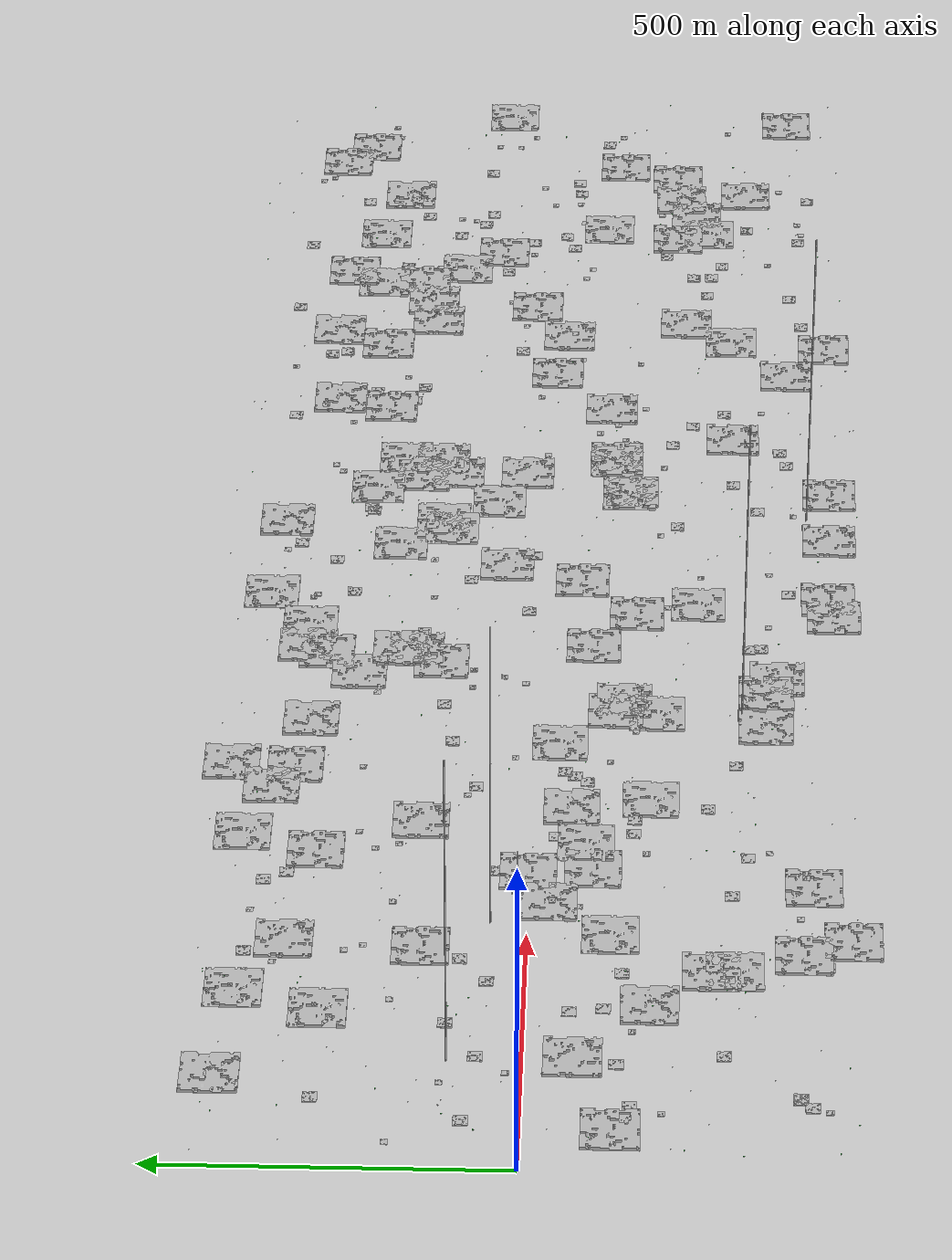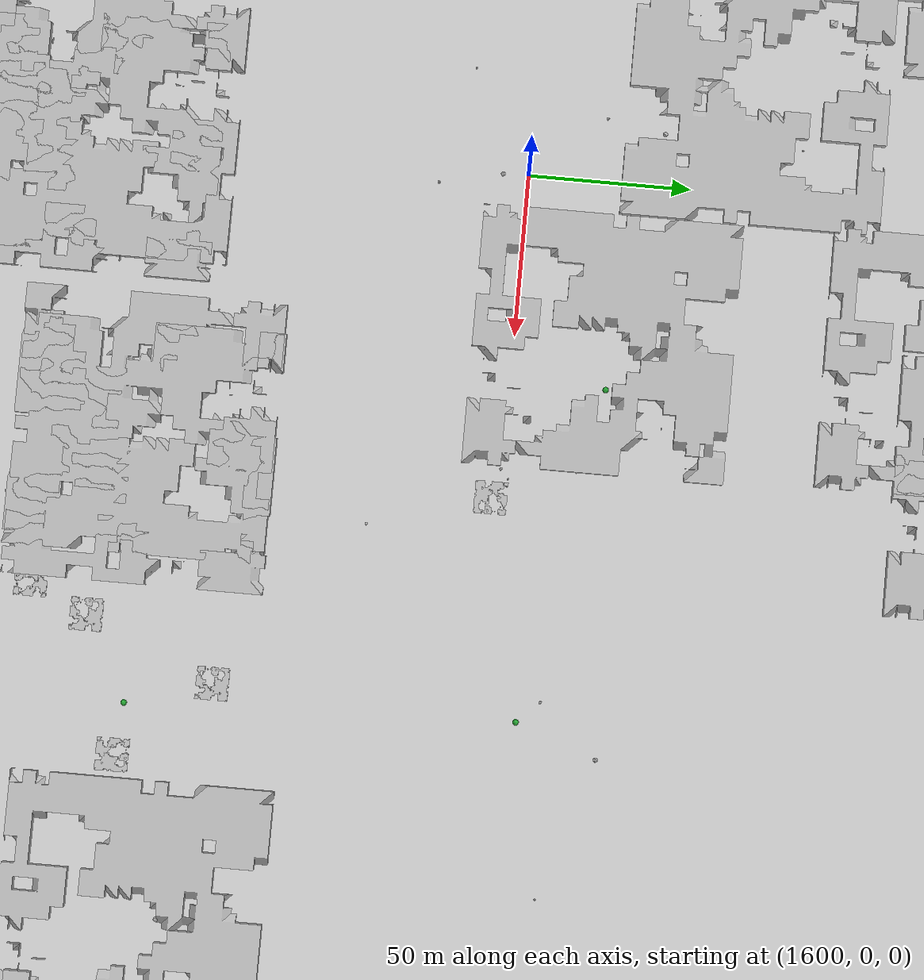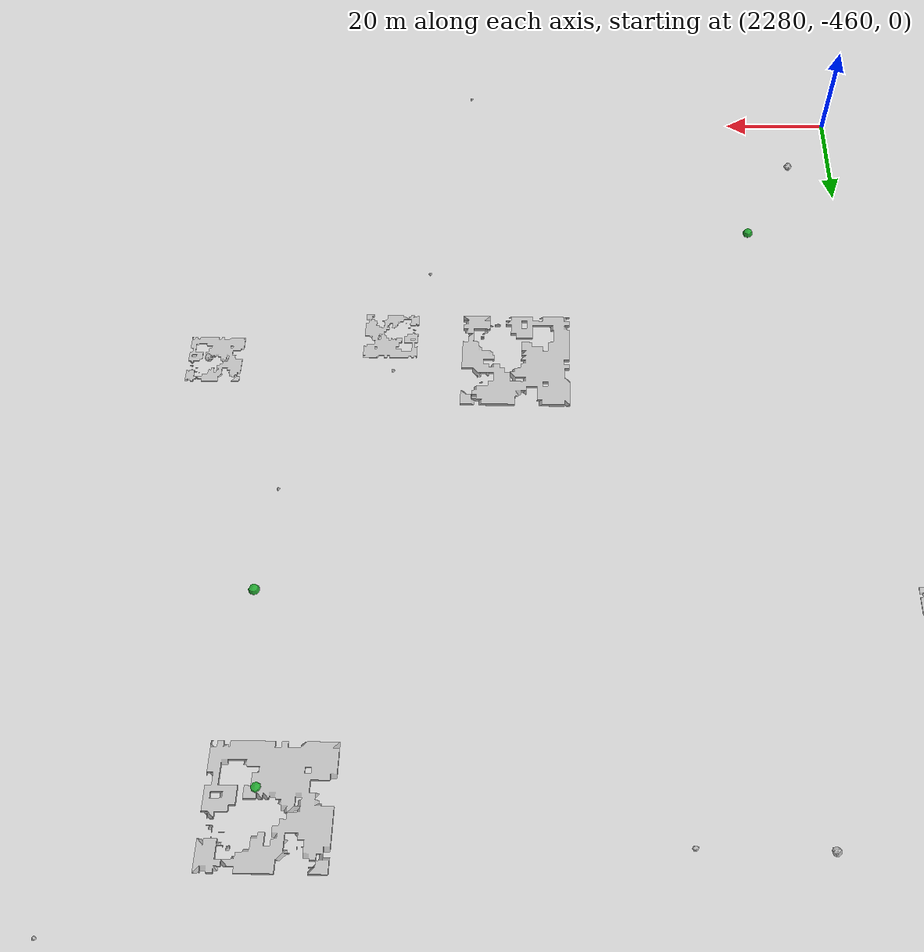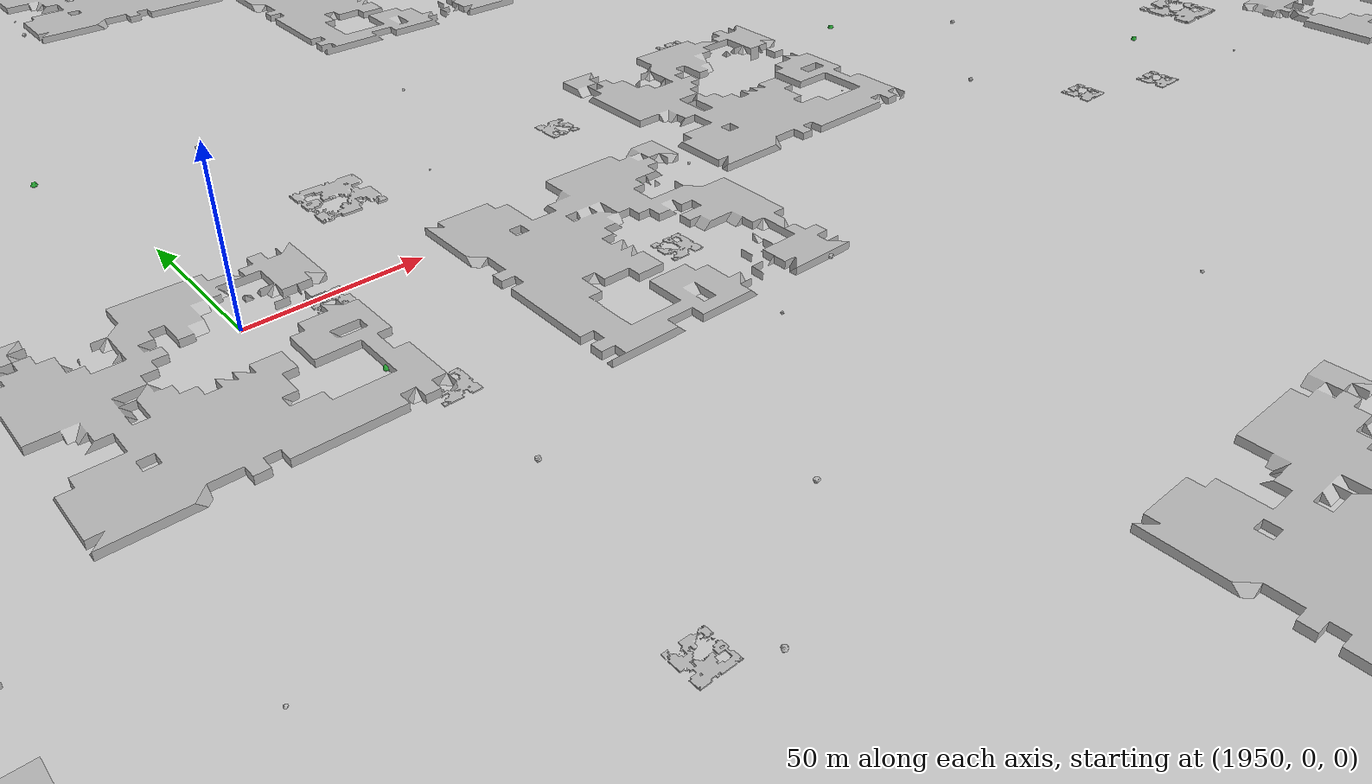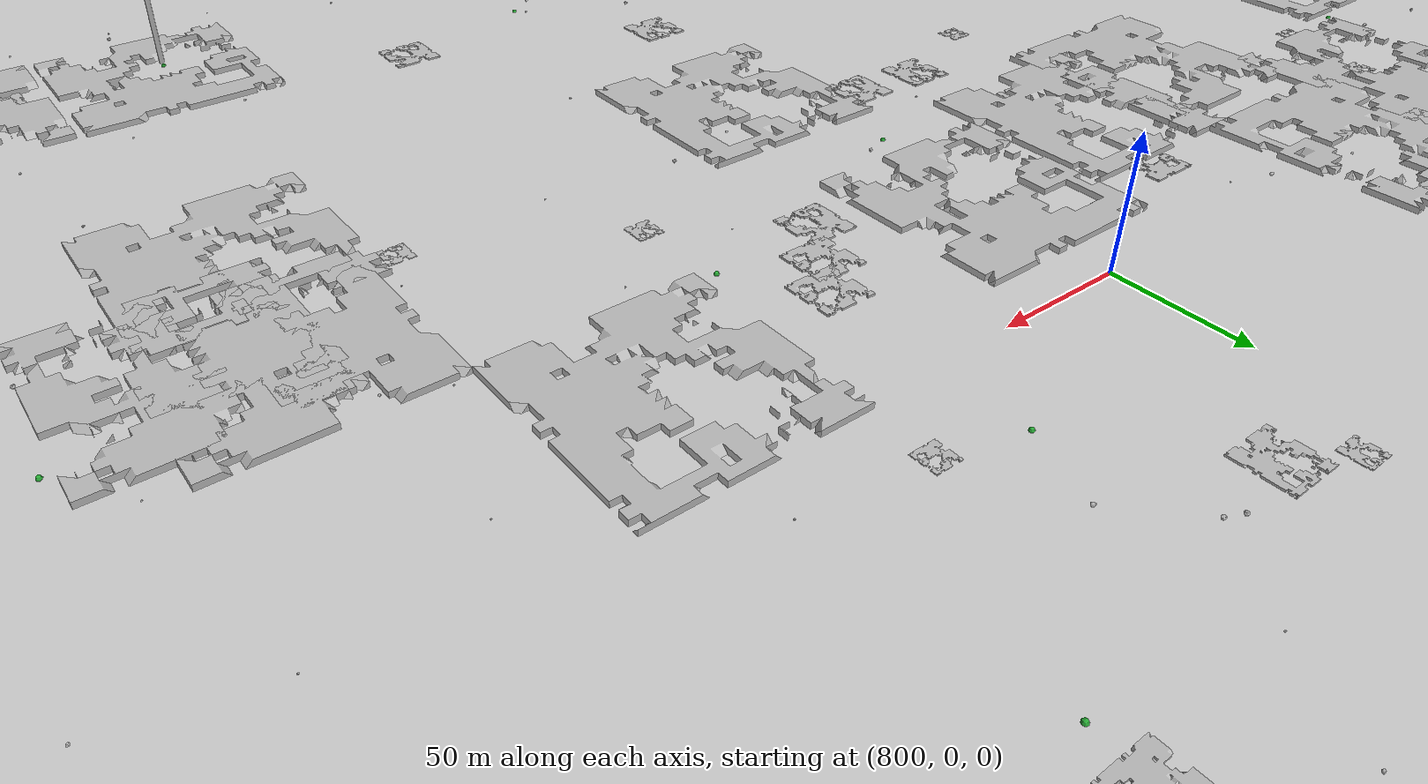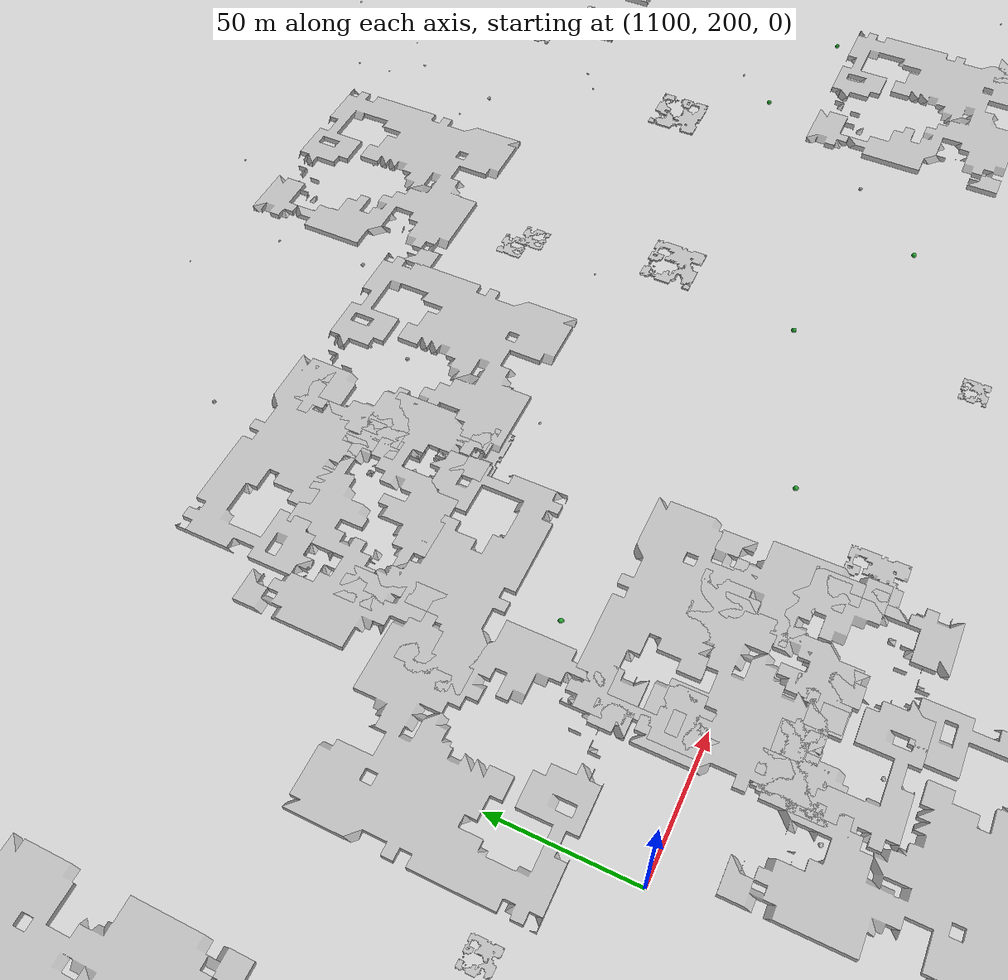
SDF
<?xml version="1.0" ?>
<sdf version="1.6">
  <world name="default">

    <include>
      <uri>model://sun</uri>
    </include>

    <include>
      <uri>model://custom_ground</uri>
    </include>

    <spherical_coordinates>
      <surface_model>EARTH_WGS84</surface_model>
      <latitude_deg>38.161479</latitude_deg>
      <longitude_deg>-122.454630</longitude_deg>
      <elevation>488.0</elevation>
      <heading_deg>90</heading_deg>
    </spherical_coordinates>

            <model name="hill1_1">
              <include>
                <uri>model://hill1</uri>
                <pose>1368.01 94.97 -1.6 0 0 3.1416</pose>
              </include>
            </model>

            <model name="hill1_2">
              <include>
                <uri>model://hill1</uri>
                <pose>1518.17 -214.74 -1.6 0 0 3.1416</pose>
              </include>
            </model>

            <model name="hill1_3">
              <include>
                <uri>model://hill1</uri>
                <pose>1556.26 254.17 -1.6 0 0 3.1416</pose>
              </include>
            </model>

            <model name="hill1_4">
              <include>
                <uri>model://hill1</uri>
                <pose>2303.28 387.19 -1.6 0 0 1.5708</pose>
              </include>
            </model>

            <model name="hill1_5">
              <include>
                <uri>model://hill1</uri>
                <pose>2219.47 -266.15 -1.6 0 0 1.5708</pose>
              </include>
            </model>

            <model name="hill1_6">
              <include>
                <uri>model://hill1</uri>
                <pose>1725.46 -372.17 -1.6 0 0 3.1416</pose>
              </include>
            </model>

            <model name="hill1_7">
              <include>
                <uri>model://hill1</uri>
                <pose>2026.72 -314.28 -1.6 0 0 1.5708</pose>
              </include>
            </model>

            <model name="hill1_8">
              <include>
                <uri>model://hill1</uri>
                <pose>169.23 -385.4 -1.6 0 0 3.1416</pose>
              </include>
            </model>

            <model name="hill1_9">
              <include>
                <uri>model://hill1</uri>
                <pose>225.41 52.87 -1.6 0 0 1.5708</pose>
              </include>
            </model>

            <model name="hill1_10">
              <include>
                <uri>model://hill1</uri>
                <pose>868.95 -36.23 -1.6 0 0 0.0</pose>
              </include>
            </model>

            <model name="hill1_11">
              <include>
                <uri>model://hill1</uri>
                <pose>315.25 95.61 -1.6 0 0 3.1416</pose>
              </include>
            </model>

            <model name="hill1_12">
              <include>
                <uri>model://hill1</uri>
                <pose>344.48 -52.04 -1.6 0 0 4.7124</pose>
              </include>
            </model>

            <model name="hill1_13">
              <include>
                <uri>model://hill1</uri>
                <pose>406.17 42.04 -1.6 0 0 3.1416</pose>
              </include>
            </model>

            <model name="hill1_14">
              <include>
                <uri>model://hill1</uri>
                <pose>2588.53 315.81 -1.6 0 0 3.1416</pose>
              </include>
            </model>

            <model name="hill1_15">
              <include>
                <uri>model://hill1</uri>
                <pose>1865.49 261.18 -1.6 0 0 1.5708</pose>
              </include>
            </model>

            <model name="hill1_16">
              <include>
                <uri>model://hill1</uri>
                <pose>734.65 -46.34 -1.6 0 0 3.1416</pose>
              </include>
            </model>

            <model name="hill1_17">
              <include>
                <uri>model://hill1</uri>
                <pose>1048.47 123.55 -1.6 0 0 3.1416</pose>
              </include>
            </model>

            <model name="hill1_18">
              <include>
                <uri>model://hill1</uri>
                <pose>829.3 70.82 -1.6 0 0 1.5708</pose>
              </include>
            </model>

            <model name="hill1_19">
              <include>
                <uri>model://hill1</uri>
                <pose>91.96 67.84 -1.6 0 0 1.5708</pose>
              </include>
            </model>

            <model name="hill1_20">
              <include>
                <uri>model://hill1</uri>
                <pose>2640.93 -75.21 -1.6 0 0 0.0</pose>
              </include>
            </model>

            <model name="hill1_21">
              <include>
                <uri>model://hill1</uri>
                <pose>444.36 399.36 -1.6 0 0 0.0</pose>
              </include>
            </model>

            <model name="hill1_22">
              <include>
                <uri>model://hill1</uri>
                <pose>2164.5 -239.71 -1.6 0 0 0.0</pose>
              </include>
            </model>

            <model name="hill1_23">
              <include>
                <uri>model://hill1</uri>
                <pose>2471.51 242.36 -1.6 0 0 4.7124</pose>
              </include>
            </model>

            <model name="hill1_24">
              <include>
                <uri>model://hill1</uri>
                <pose>1541.65 -336.57 -1.6 0 0 1.5708</pose>
              </include>
            </model>

            <model name="hill1_25">
              <include>
                <uri>model://hill1</uri>
                <pose>233.97 -117.8 -1.6 0 0 4.7124</pose>
              </include>
            </model>

            <model name="hill1_26">
              <include>
                <uri>model://hill1</uri>
                <pose>134.56 290.23 -1.6 0 0 0.0</pose>
              </include>
            </model>

            <model name="hill1_27">
              <include>
                <uri>model://hill1</uri>
                <pose>776.35 -137.46 -1.6 0 0 4.7124</pose>
              </include>
            </model>

            <model name="hill1_28">
              <include>
                <uri>model://hill1</uri>
                <pose>2442.81 320.91 -1.6 0 0 0.0</pose>
              </include>
            </model>

            <model name="hill1_29">
              <include>
                <uri>model://hill1</uri>
                <pose>1459.08 375.19 -1.6 0 0 4.7124</pose>
              </include>
            </model>

            <model name="hill1_30">
              <include>
                <uri>model://hill1</uri>
                <pose>1199.17 -339.25 -1.6 0 0 3.1416</pose>
              </include>
            </model>

            <model name="hill1_31">
              <include>
                <uri>model://hill1</uri>
                <pose>1197.56 -302.18 -1.6 0 0 4.7124</pose>
              </include>
            </model>

            <model name="hill1_32">
              <include>
                <uri>model://hill1</uri>
                <pose>2177.06 -392.09 -1.6 0 0 3.1416</pose>
              </include>
            </model>

            <model name="hill1_33">
              <include>
                <uri>model://hill1</uri>
                <pose>429.05 -122.81 -1.6 0 0 4.7124</pose>
              </include>
            </model>

            <model name="hill1_34">
              <include>
                <uri>model://hill1</uri>
                <pose>2283.03 -194.09 -1.6 0 0 1.5708</pose>
              </include>
            </model>

            <model name="hill1_35">
              <include>
                <uri>model://hill1</uri>
                <pose>428.68 -405.71 -1.6 0 0 0.0</pose>
              </include>
            </model>

            <model name="hill1_36">
              <include>
                <uri>model://hill1</uri>
                <pose>1860.83 219.48 -1.6 0 0 4.7124</pose>
              </include>
            </model>

            <model name="hill1_37">
              <include>
                <uri>model://hill1</uri>
                <pose>908.93 -282.34 -1.6 0 0 4.7124</pose>
              </include>
            </model>

            <model name="hill1_38">
              <include>
                <uri>model://hill1</uri>
                <pose>672.29 -317.43 -1.6 0 0 1.5708</pose>
              </include>
            </model>

            <model name="hill1_39">
              <include>
                <uri>model://hill1</uri>
                <pose>604.92 361.75 -1.6 0 0 1.5708</pose>
              </include>
            </model>

            <model name="hill1_40">
              <include>
                <uri>model://hill1</uri>
                <pose>1066.12 -337.3 -1.6 0 0 4.7124</pose>
              </include>
            </model>

            <model name="hill1_41">
              <include>
                <uri>model://hill1</uri>
                <pose>2407.77 113.13 -1.6 0 0 0.0</pose>
              </include>
            </model>

            <model name="hill1_42">
              <include>
                <uri>model://hill1</uri>
                <pose>937.9 128.83 -1.6 0 0 0.0</pose>
              </include>
            </model>

            <model name="hill1_43">
              <include>
                <uri>model://hill1</uri>
                <pose>1395.64 319.9 -1.6 0 0 0.0</pose>
              </include>
            </model>

            <model name="hill1_44">
              <include>
                <uri>model://hill1</uri>
                <pose>2238.63 -218.46 -1.6 0 0 4.7124</pose>
              </include>
            </model>

            <model name="hill1_45">
              <include>
                <uri>model://hill1</uri>
                <pose>724.34 -155.61 -1.6 0 0 1.5708</pose>
              </include>
            </model>

            <model name="hill1_46">
              <include>
                <uri>model://hill1</uri>
                <pose>2306.26 -23.12 -1.6 0 0 0.0</pose>
              </include>
            </model>

            <model name="hill1_47">
              <include>
                <uri>model://hill1</uri>
                <pose>1414.76 19.43 -1.6 0 0 0.0</pose>
              </include>
            </model>

            <model name="hill1_48">
              <include>
                <uri>model://hill1</uri>
                <pose>858.35 -50.69 -1.6 0 0 0.0</pose>
              </include>
            </model>

            <model name="hill1_49">
              <include>
                <uri>model://hill1</uri>
                <pose>2146.43 209.55 -1.6 0 0 0.0</pose>
              </include>
            </model>

            <model name="hill1_50">
              <include>
                <uri>model://hill1</uri>
                <pose>2261.27 247.64 -1.6 0 0 4.7124</pose>
              </include>
            </model>

            <model name="hill1_51">
              <include>
                <uri>model://hill1</uri>
                <pose>633.18 53.56 -1.6 0 0 0.0</pose>
              </include>
            </model>

            <model name="hill1_52">
              <include>
                <uri>model://hill1</uri>
                <pose>2339.05 164.78 -1.6 0 0 0.0</pose>
              </include>
            </model>

            <model name="hill1_53">
              <include>
                <uri>model://hill1</uri>
                <pose>2542.11 118.9 -1.6 0 0 0.0</pose>
              </include>
            </model>

            <model name="hill1_54">
              <include>
                <uri>model://hill1</uri>
                <pose>2247.09 63.33 -1.6 0 0 3.1416</pose>
              </include>
            </model>

            <model name="hill1_55">
              <include>
                <uri>model://hill1</uri>
                <pose>254.34 -282.9 -1.6 0 0 3.1416</pose>
              </include>
            </model>

            <model name="hill1_56">
              <include>
                <uri>model://hill1</uri>
                <pose>865.04 -68.93 -1.6 0 0 4.7124</pose>
              </include>
            </model>

            <model name="hill1_57">
              <include>
                <uri>model://hill1</uri>
                <pose>2243.52 178.66 -1.6 0 0 0.0</pose>
              </include>
            </model>

            <model name="hill1_58">
              <include>
                <uri>model://hill1</uri>
                <pose>2093.54 -409.95 -1.6 0 0 3.1416</pose>
              </include>
            </model>

            <model name="hill1_59">
              <include>
                <uri>model://hill1</uri>
                <pose>2581.09 321.36 -1.6 0 0 1.5708</pose>
              </include>
            </model>

            <model name="hill1_60">
              <include>
                <uri>model://hill1</uri>
                <pose>150.2 -401.21 -1.6 0 0 3.1416</pose>
              </include>
            </model>

            <model name="hill1_61">
              <include>
                <uri>model://hill1</uri>
                <pose>1202.58 319.01 -1.6 0 0 0.0</pose>
              </include>
            </model>

            <model name="hill1_62">
              <include>
                <uri>model://hill1</uri>
                <pose>2483.82 -405.28 -1.6 0 0 4.7124</pose>
              </include>
            </model>

            <model name="hill1_63">
              <include>
                <uri>model://hill1</uri>
                <pose>426.74 -248.09 -1.6 0 0 4.7124</pose>
              </include>
            </model>

            <model name="hill1_64">
              <include>
                <uri>model://hill1</uri>
                <pose>351.71 -98.8 -1.6 0 0 4.7124</pose>
              </include>
            </model>

            <model name="hill1_65">
              <include>
                <uri>model://hill1</uri>
                <pose>622.22 350.05 -1.6 0 0 0.0</pose>
              </include>
            </model>

            <model name="hill1_66">
              <include>
                <uri>model://hill1</uri>
                <pose>1548.9 249.48 -1.6 0 0 3.1416</pose>
              </include>
            </model>

            <model name="hill1_67">
              <include>
                <uri>model://hill1</uri>
                <pose>2341.61 42.2 -1.6 0 0 4.7124</pose>
              </include>
            </model>

            <model name="hill1_68">
              <include>
                <uri>model://hill1</uri>
                <pose>2340.81 -29.23 -1.6 0 0 1.5708</pose>
              </include>
            </model>

            <model name="hill1_69">
              <include>
                <uri>model://hill1</uri>
                <pose>1614.27 -279.91 -1.6 0 0 0.0</pose>
              </include>
            </model>

            <model name="hill1_70">
              <include>
                <uri>model://hill1</uri>
                <pose>126.95 -155.98 -1.6 0 0 1.5708</pose>
              </include>
            </model>

            <model name="hill1_71">
              <include>
                <uri>model://hill1</uri>
                <pose>2009.41 33.69 -1.6 0 0 3.1416</pose>
              </include>
            </model>

            <model name="hill1_72">
              <include>
                <uri>model://hill1</uri>
                <pose>1341.72 -361.92 -1.6 0 0 4.7124</pose>
              </include>
            </model>

            <model name="hill1_73">
              <include>
                <uri>model://hill1</uri>
                <pose>1209.9 160.48 -1.6 0 0 1.5708</pose>
              </include>
            </model>

            <model name="hill1_74">
              <include>
                <uri>model://hill1</uri>
                <pose>2353.82 -388.44 -1.6 0 0 4.7124</pose>
              </include>
            </model>

            <model name="hill1_75">
              <include>
                <uri>model://hill1</uri>
                <pose>2276.13 -283.37 -1.6 0 0 3.1416</pose>
              </include>
            </model>

            <model name="hill1_76">
              <include>
                <uri>model://hill1</uri>
                <pose>1877.61 186.29 -1.6 0 0 1.5708</pose>
              </include>
            </model>

            <model name="hill1_77">
              <include>
                <uri>model://hill1</uri>
                <pose>1287.87 25.56 -1.6 0 0 4.7124</pose>
              </include>
            </model>

            <model name="hill1_78">
              <include>
                <uri>model://hill1</uri>
                <pose>2000.73 333.62 -1.6 0 0 4.7124</pose>
              </include>
            </model>

            <model name="hill1_79">
              <include>
                <uri>model://hill1</uri>
                <pose>784.89 -260.93 -1.6 0 0 1.5708</pose>
              </include>
            </model>

            <model name="hill1_80">
              <include>
                <uri>model://hill1</uri>
                <pose>2436.18 269.89 -1.6 0 0 0.0</pose>
              </include>
            </model>

            <model name="hill1_81">
              <include>
                <uri>model://hill1</uri>
                <pose>1743.66 -186.68 -1.6 0 0 4.7124</pose>
              </include>
            </model>

            <model name="hill1_82">
              <include>
                <uri>model://hill1</uri>
                <pose>2369.8 -304.66 -1.6 0 0 0.0</pose>
              </include>
            </model>

            <model name="hill1_83">
              <include>
                <uri>model://hill1</uri>
                <pose>120.61 -152.16 -1.6 0 0 3.1416</pose>
              </include>
            </model>

            <model name="hill1_84">
              <include>
                <uri>model://hill1</uri>
                <pose>1732.41 -327.13 -1.6 0 0 1.5708</pose>
              </include>
            </model>

            <model name="hill1_85">
              <include>
                <uri>model://hill1</uri>
                <pose>146.43 -364.51 -1.6 0 0 0.0</pose>
              </include>
            </model>

            <model name="hill1_86">
              <include>
                <uri>model://hill1</uri>
                <pose>2396.69 124.64 -1.6 0 0 4.7124</pose>
              </include>
            </model>

            <model name="hill1_87">
              <include>
                <uri>model://hill1</uri>
                <pose>2398.93 199.31 -1.6 0 0 1.5708</pose>
              </include>
            </model>

            <model name="hill1_88">
              <include>
                <uri>model://hill1</uri>
                <pose>434.35 80.65 -1.6 0 0 1.5708</pose>
              </include>
            </model>

            <model name="hill1_89">
              <include>
                <uri>model://hill1</uri>
                <pose>1837.18 364.84 -1.6 0 0 4.7124</pose>
              </include>
            </model>

            <model name="hill1_90">
              <include>
                <uri>model://hill1</uri>
                <pose>2070.7 -266.58 -1.6 0 0 4.7124</pose>
              </include>
            </model>

            <model name="hill1_91">
              <include>
                <uri>model://hill1</uri>
                <pose>1311.86 269.42 -1.6 0 0 1.5708</pose>
              </include>
            </model>

            <model name="hill1_92">
              <include>
                <uri>model://hill1</uri>
                <pose>1813.12 -286.58 -1.6 0 0 1.5708</pose>
              </include>
            </model>

            <model name="hill1_93">
              <include>
                <uri>model://hill1</uri>
                <pose>584.99 -294.76 -1.6 0 0 1.5708</pose>
              </include>
            </model>

            <model name="hill1_94">
              <include>
                <uri>model://hill1</uri>
                <pose>2479.09 -31.06 -1.6 0 0 0.0</pose>
              </include>
            </model>

            <model name="hill1_95">
              <include>
                <uri>model://hill1</uri>
                <pose>1797.77 -237.44 -1.6 0 0 3.1416</pose>
              </include>
            </model>

            <model name="hill1_96">
              <include>
                <uri>model://hill1</uri>
                <pose>2132.19 397.02 -1.6 0 0 3.1416</pose>
              </include>
            </model>

            <model name="hill1_97">
              <include>
                <uri>model://hill1</uri>
                <pose>1812.96 385.18 -1.6 0 0 3.1416</pose>
              </include>
            </model>

            <model name="hill1_98">
              <include>
                <uri>model://hill1</uri>
                <pose>1972.32 338.25 -1.6 0 0 1.5708</pose>
              </include>
            </model>

            <model name="hill1_99">
              <include>
                <uri>model://hill1</uri>
                <pose>1689.12 -382.06 -1.6 0 0 3.1416</pose>
              </include>
            </model>

            <model name="hill1_100">
              <include>
                <uri>model://hill1</uri>
                <pose>2513.53 -47.04 -1.6 0 0 1.5708</pose>
              </include>
            </model>

            <model name="hill2_1">
              <include>
                <uri>model://hill2</uri>
                <pose>1218.78 163.26 -6 0 0 3.1416</pose>
              </include>
            </model>

            <model name="hill2_2">
              <include>
                <uri>model://hill2</uri>
                <pose>1037.75 285.41 -6 0 0 3.1416</pose>
              </include>
            </model>

            <model name="hill2_3">
              <include>
                <uri>model://hill2</uri>
                <pose>1322.14 -21.97 -6 0 0 0.0</pose>
              </include>
            </model>

            <model name="hill2_4">
              <include>
                <uri>model://hill2</uri>
                <pose>1454.66 99.32 -6 0 0 1.5708</pose>
              </include>
            </model>

            <model name="hill2_5">
              <include>
                <uri>model://hill2</uri>
                <pose>390.68 -212.24 -6 0 0 3.1416</pose>
              </include>
            </model>

            <model name="hill2_6">
              <include>
                <uri>model://hill2</uri>
                <pose>332.4 358.44 -6 0 0 1.5708</pose>
              </include>
            </model>

            <model name="hill2_7">
              <include>
                <uri>model://hill2</uri>
                <pose>874.42 333.14 -6 0 0 3.1416</pose>
              </include>
            </model>

            <model name="hill2_8">
              <include>
                <uri>model://hill2</uri>
                <pose>1478.64 113.26 -6 0 0 1.5708</pose>
              </include>
            </model>

            <model name="hill2_9">
              <include>
                <uri>model://hill2</uri>
                <pose>1127.29 352.35 -6 0 0 0.0</pose>
              </include>
            </model>

            <model name="hill2_10">
              <include>
                <uri>model://hill2</uri>
                <pose>2129.26 221.63 -6 0 0 4.7124</pose>
              </include>
            </model>

            <model name="hill2_11">
              <include>
                <uri>model://hill2</uri>
                <pose>1217.09 219.57 -6 0 0 4.7124</pose>
              </include>
            </model>

            <model name="hill2_12">
              <include>
                <uri>model://hill2</uri>
                <pose>2698.0 37.76 -6 0 0 1.5708</pose>
              </include>
            </model>

            <model name="hill2_13">
              <include>
                <uri>model://hill2</uri>
                <pose>1069.54 -77.55 -6 0 0 4.7124</pose>
              </include>
            </model>

            <model name="hill2_14">
              <include>
                <uri>model://hill2</uri>
                <pose>1095.49 -89.2 -6 0 0 4.7124</pose>
              </include>
            </model>

            <model name="hill2_15">
              <include>
                <uri>model://hill2</uri>
                <pose>2336.06 -128.34 -6 0 0 1.5708</pose>
              </include>
            </model>

            <model name="hill2_16">
              <include>
                <uri>model://hill2</uri>
                <pose>50.04 -80.63 -6 0 0 0.0</pose>
              </include>
            </model>

            <model name="hill2_17">
              <include>
                <uri>model://hill2</uri>
                <pose>425.86 -343.08 -6 0 0 0.0</pose>
              </include>
            </model>

            <model name="hill2_18">
              <include>
                <uri>model://hill2</uri>
                <pose>798.7 195.73 -6 0 0 4.7124</pose>
              </include>
            </model>

            <model name="hill2_19">
              <include>
                <uri>model://hill2</uri>
                <pose>1977.02 300.4 -6 0 0 0.0</pose>
              </include>
            </model>

            <model name="hill2_20">
              <include>
                <uri>model://hill2</uri>
                <pose>1562.22 -94.23 -6 0 0 0.0</pose>
              </include>
            </model>

            <model name="hill2_21">
              <include>
                <uri>model://hill2</uri>
                <pose>775.3 -209.09 -6 0 0 1.5708</pose>
              </include>
            </model>

            <model name="hill2_22">
              <include>
                <uri>model://hill2</uri>
                <pose>846.19 382.99 -6 0 0 0.0</pose>
              </include>
            </model>

            <model name="hill2_23">
              <include>
                <uri>model://hill2</uri>
                <pose>2189.91 231.36 -6 0 0 4.7124</pose>
              </include>
            </model>

            <model name="hill2_24">
              <include>
                <uri>model://hill2</uri>
                <pose>463.26 -155.57 -6 0 0 1.5708</pose>
              </include>
            </model>

            <model name="hill2_25">
              <include>
                <uri>model://hill2</uri>
                <pose>1994.42 -326.89 -6 0 0 1.5708</pose>
              </include>
            </model>

            <model name="hill2_26">
              <include>
                <uri>model://hill2</uri>
                <pose>2683.14 -342.31 -6 0 0 0.0</pose>
              </include>
            </model>

            <model name="hill2_27">
              <include>
                <uri>model://hill2</uri>
                <pose>646.43 342.69 -6 0 0 0.0</pose>
              </include>
            </model>

            <model name="hill2_28">
              <include>
                <uri>model://hill2</uri>
                <pose>1198.63 301.53 -6 0 0 1.5708</pose>
              </include>
            </model>

            <model name="hill2_29">
              <include>
                <uri>model://hill2</uri>
                <pose>1280.72 -389.97 -6 0 0 0.0</pose>
              </include>
            </model>

            <model name="hill2_30">
              <include>
                <uri>model://hill2</uri>
                <pose>2161.47 235.4 -6 0 0 1.5708</pose>
              </include>
            </model>

            <model name="hill2_31">
              <include>
                <uri>model://hill2</uri>
                <pose>1157.31 301.32 -6 0 0 4.7124</pose>
              </include>
            </model>

            <model name="hill2_32">
              <include>
                <uri>model://hill2</uri>
                <pose>834.92 -97.77 -6 0 0 3.1416</pose>
              </include>
            </model>

            <model name="hill2_33">
              <include>
                <uri>model://hill2</uri>
                <pose>1564.11 217.54 -6 0 0 1.5708</pose>
              </include>
            </model>

            <model name="hill2_34">
              <include>
                <uri>model://hill2</uri>
                <pose>2538.07 -72.8 -6 0 0 0.0</pose>
              </include>
            </model>

            <model name="hill2_35">
              <include>
                <uri>model://hill2</uri>
                <pose>1234.9 -398.11 -6 0 0 0.0</pose>
              </include>
            </model>

            <model name="hill2_36">
              <include>
                <uri>model://hill2</uri>
                <pose>612.26 -49.26 -6 0 0 0.0</pose>
              </include>
            </model>

            <model name="hill2_37">
              <include>
                <uri>model://hill2</uri>
                <pose>1220.93 303.2 -6 0 0 3.1416</pose>
              </include>
            </model>

            <model name="hill2_38">
              <include>
                <uri>model://hill2</uri>
                <pose>2518.2 202.64 -6 0 0 3.1416</pose>
              </include>
            </model>

            <model name="hill2_39">
              <include>
                <uri>model://hill2</uri>
                <pose>1977.97 -394.26 -6 0 0 0.0</pose>
              </include>
            </model>

            <model name="hill2_40">
              <include>
                <uri>model://hill2</uri>
                <pose>1646.08 177.75 -6 0 0 1.5708</pose>
              </include>
            </model>

            <model name="hill2_41">
              <include>
                <uri>model://hill2</uri>
                <pose>2514.15 -247.22 -6 0 0 3.1416</pose>
              </include>
            </model>

            <model name="hill2_42">
              <include>
                <uri>model://hill2</uri>
                <pose>1656.32 -68.87 -6 0 0 0.0</pose>
              </include>
            </model>

            <model name="hill2_43">
              <include>
                <uri>model://hill2</uri>
                <pose>1792.89 -250.13 -6 0 0 4.7124</pose>
              </include>
            </model>

            <model name="hill2_44">
              <include>
                <uri>model://hill2</uri>
                <pose>1977.85 -334.68 -6 0 0 4.7124</pose>
              </include>
            </model>

            <model name="hill2_45">
              <include>
                <uri>model://hill2</uri>
                <pose>2543.38 392.96 -6 0 0 0.0</pose>
              </include>
            </model>

            <model name="hill2_46">
              <include>
                <uri>model://hill2</uri>
                <pose>1517.05 -395.31 -6 0 0 4.7124</pose>
              </include>
            </model>

            <model name="hill2_47">
              <include>
                <uri>model://hill2</uri>
                <pose>1726.09 198.43 -6 0 0 4.7124</pose>
              </include>
            </model>

            <model name="hill2_48">
              <include>
                <uri>model://hill2</uri>
                <pose>1550.03 350.49 -6 0 0 3.1416</pose>
              </include>
            </model>

            <model name="hill2_49">
              <include>
                <uri>model://hill2</uri>
                <pose>907.88 -76.88 -6 0 0 1.5708</pose>
              </include>
            </model>

            <model name="hill2_50">
              <include>
                <uri>model://hill2</uri>
                <pose>1278.11 363.33 -6 0 0 1.5708</pose>
              </include>
            </model>

            <model name="hill2_51">
              <include>
                <uri>model://hill2</uri>
                <pose>2088.01 9.81 -6 0 0 4.7124</pose>
              </include>
            </model>

            <model name="hill2_52">
              <include>
                <uri>model://hill2</uri>
                <pose>614.96 -69.54 -6 0 0 3.1416</pose>
              </include>
            </model>

            <model name="hill2_53">
              <include>
                <uri>model://hill2</uri>
                <pose>387.49 -327.93 -6 0 0 1.5708</pose>
              </include>
            </model>

            <model name="hill2_54">
              <include>
                <uri>model://hill2</uri>
                <pose>2593.55 347.74 -6 0 0 0.0</pose>
              </include>
            </model>

            <model name="hill2_55">
              <include>
                <uri>model://hill2</uri>
                <pose>1261.49 -276.06 -6 0 0 1.5708</pose>
              </include>
            </model>

            <model name="hill2_56">
              <include>
                <uri>model://hill2</uri>
                <pose>1897.07 27.7 -6 0 0 0.0</pose>
              </include>
            </model>

            <model name="hill2_57">
              <include>
                <uri>model://hill2</uri>
                <pose>1599.22 228.24 -6 0 0 0.0</pose>
              </include>
            </model>

            <model name="hill2_58">
              <include>
                <uri>model://hill2</uri>
                <pose>1152.34 -41.7 -6 0 0 0.0</pose>
              </include>
            </model>

            <model name="hill2_59">
              <include>
                <uri>model://hill2</uri>
                <pose>466.81 -216.39 -6 0 0 4.7124</pose>
              </include>
            </model>

            <model name="hill2_60">
              <include>
                <uri>model://hill2</uri>
                <pose>1236.88 -104.63 -6 0 0 0.0</pose>
              </include>
            </model>

            <model name="hill2_61">
              <include>
                <uri>model://hill2</uri>
                <pose>1107.1 182.49 -6 0 0 0.0</pose>
              </include>
            </model>

            <model name="hill2_62">
              <include>
                <uri>model://hill2</uri>
                <pose>2095.27 299.31 -6 0 0 3.1416</pose>
              </include>
            </model>

            <model name="hill2_63">
              <include>
                <uri>model://hill2</uri>
                <pose>230.43 377.11 -6 0 0 3.1416</pose>
              </include>
            </model>

            <model name="hill2_64">
              <include>
                <uri>model://hill2</uri>
                <pose>1038.87 -295.92 -6 0 0 0.0</pose>
              </include>
            </model>

            <model name="hill2_65">
              <include>
                <uri>model://hill2</uri>
                <pose>1528.9 29.37 -6 0 0 1.5708</pose>
              </include>
            </model>

            <model name="hill2_66">
              <include>
                <uri>model://hill2</uri>
                <pose>458.14 -412.29 -6 0 0 0.0</pose>
              </include>
            </model>

            <model name="hill2_67">
              <include>
                <uri>model://hill2</uri>
                <pose>671.63 -118.26 -6 0 0 1.5708</pose>
              </include>
            </model>

            <model name="hill2_68">
              <include>
                <uri>model://hill2</uri>
                <pose>1793.2 286.73 -6 0 0 0.0</pose>
              </include>
            </model>

            <model name="hill2_69">
              <include>
                <uri>model://hill2</uri>
                <pose>603.68 41.63 -6 0 0 0.0</pose>
              </include>
            </model>

            <model name="hill2_70">
              <include>
                <uri>model://hill2</uri>
                <pose>1690.66 66.58 -6 0 0 4.7124</pose>
              </include>
            </model>

            <model name="hill2_71">
              <include>
                <uri>model://hill2</uri>
                <pose>577.54 -358.88 -6 0 0 0.0</pose>
              </include>
            </model>

            <model name="hill2_72">
              <include>
                <uri>model://hill2</uri>
                <pose>523.25 374.39 -6 0 0 4.7124</pose>
              </include>
            </model>

            <model name="hill2_73">
              <include>
                <uri>model://hill2</uri>
                <pose>278.89 -29.19 -6 0 0 4.7124</pose>
              </include>
            </model>

            <model name="hill2_74">
              <include>
                <uri>model://hill2</uri>
                <pose>684.12 368.14 -6 0 0 1.5708</pose>
              </include>
            </model>

            <model name="hill2_75">
              <include>
                <uri>model://hill2</uri>
                <pose>928.58 393.91 -6 0 0 3.1416</pose>
              </include>
            </model>

            <model name="hill2_76">
              <include>
                <uri>model://hill2</uri>
                <pose>983.33 -216.51 -6 0 0 1.5708</pose>
              </include>
            </model>

            <model name="hill2_77">
              <include>
                <uri>model://hill2</uri>
                <pose>2464.86 -192.87 -6 0 0 4.7124</pose>
              </include>
            </model>

            <model name="hill2_78">
              <include>
                <uri>model://hill2</uri>
                <pose>1411.75 175.76 -6 0 0 1.5708</pose>
              </include>
            </model>

            <model name="hill2_79">
              <include>
                <uri>model://hill2</uri>
                <pose>2206.33 101.43 -6 0 0 1.5708</pose>
              </include>
            </model>

            <model name="hill2_80">
              <include>
                <uri>model://hill2</uri>
                <pose>1440.77 91.42 -6 0 0 4.7124</pose>
              </include>
            </model>

            <model name="hill2_81">
              <include>
                <uri>model://hill2</uri>
                <pose>1034.11 -375.75 -6 0 0 3.1416</pose>
              </include>
            </model>

            <model name="hill2_82">
              <include>
                <uri>model://hill2</uri>
                <pose>1155.86 -313.18 -6 0 0 4.7124</pose>
              </include>
            </model>

            <model name="hill2_83">
              <include>
                <uri>model://hill2</uri>
                <pose>2502.25 -160.14 -6 0 0 0.0</pose>
              </include>
            </model>

            <model name="hill2_84">
              <include>
                <uri>model://hill2</uri>
                <pose>2312.51 238.3 -6 0 0 1.5708</pose>
              </include>
            </model>

            <model name="hill2_85">
              <include>
                <uri>model://hill2</uri>
                <pose>2196.06 365.45 -6 0 0 0.0</pose>
              </include>
            </model>

            <model name="hill2_86">
              <include>
                <uri>model://hill2</uri>
                <pose>2129.29 -176.81 -6 0 0 4.7124</pose>
              </include>
            </model>

            <model name="hill2_87">
              <include>
                <uri>model://hill2</uri>
                <pose>2530.38 -273.31 -6 0 0 4.7124</pose>
              </include>
            </model>

            <model name="hill2_88">
              <include>
                <uri>model://hill2</uri>
                <pose>2169.77 249.2 -6 0 0 0.0</pose>
              </include>
            </model>

            <model name="hill2_89">
              <include>
                <uri>model://hill2</uri>
                <pose>432.32 186.47 -6 0 0 0.0</pose>
              </include>
            </model>

            <model name="hill2_90">
              <include>
                <uri>model://hill2</uri>
                <pose>1555.44 -169.51 -6 0 0 1.5708</pose>
              </include>
            </model>

            <model name="hill2_91">
              <include>
                <uri>model://hill2</uri>
                <pose>2094.3 64.15 -6 0 0 0.0</pose>
              </include>
            </model>

            <model name="hill2_92">
              <include>
                <uri>model://hill2</uri>
                <pose>1875.1 -60.87 -6 0 0 4.7124</pose>
              </include>
            </model>

            <model name="hill2_93">
              <include>
                <uri>model://hill2</uri>
                <pose>1646.04 -149.44 -6 0 0 1.5708</pose>
              </include>
            </model>

            <model name="hill2_94">
              <include>
                <uri>model://hill2</uri>
                <pose>1561.34 -396.02 -6 0 0 0.0</pose>
              </include>
            </model>

            <model name="hill2_95">
              <include>
                <uri>model://hill2</uri>
                <pose>2325.51 -292.09 -6 0 0 1.5708</pose>
              </include>
            </model>

            <model name="hill2_96">
              <include>
                <uri>model://hill2</uri>
                <pose>2260.6 122.81 -6 0 0 0.0</pose>
              </include>
            </model>

            <model name="hill2_97">
              <include>
                <uri>model://hill2</uri>
                <pose>1895.19 287.33 -6 0 0 3.1416</pose>
              </include>
            </model>

            <model name="hill2_98">
              <include>
                <uri>model://hill2</uri>
                <pose>292.25 240.63 -6 0 0 1.5708</pose>
              </include>
            </model>

            <model name="hill2_99">
              <include>
                <uri>model://hill2</uri>
                <pose>2309.94 -161.43 -6 0 0 0.0</pose>
              </include>
            </model>

            <model name="hill2_100">
              <include>
                <uri>model://hill2</uri>
                <pose>1688.71 174.47 -6 0 0 4.7124</pose>
              </include>
            </model>

            <model name="hill3_1">
              <include>
                <uri>model://hill3</uri>
                <pose>1129.07 88.44 -1 0 0 3.1416</pose>
              </include>
            </model>

            <model name="hill3_2">
              <include>
                <uri>model://hill3</uri>
                <pose>1860.46 5.7 -1 0 0 1.5708</pose>
              </include>
            </model>

            <model name="hill3_3">
              <include>
                <uri>model://hill3</uri>
                <pose>2394.67 -392.77 -1 0 0 0.0</pose>
              </include>
            </model>

            <model name="hill3_4">
              <include>
                <uri>model://hill3</uri>
                <pose>1240.41 -336.12 -1 0 0 0.0</pose>
              </include>
            </model>

            <model name="hill3_5">
              <include>
                <uri>model://hill3</uri>
                <pose>540.54 -374.22 -1 0 0 0.0</pose>
              </include>
            </model>

            <model name="hill3_6">
              <include>
                <uri>model://hill3</uri>
                <pose>2372.12 -408.74 -1 0 0 3.1416</pose>
              </include>
            </model>

            <model name="hill3_7">
              <include>
                <uri>model://hill3</uri>
                <pose>982.78 -142.08 -1 0 0 4.7124</pose>
              </include>
            </model>

            <model name="hill3_8">
              <include>
                <uri>model://hill3</uri>
                <pose>1751.11 -127.57 -1 0 0 3.1416</pose>
              </include>
            </model>

            <model name="hill3_9">
              <include>
                <uri>model://hill3</uri>
                <pose>2668.09 262.09 -1 0 0 3.1416</pose>
              </include>
            </model>

            <model name="hill3_10">
              <include>
                <uri>model://hill3</uri>
                <pose>1668.99 329.49 -1 0 0 4.7124</pose>
              </include>
            </model>

            <model name="hill3_11">
              <include>
                <uri>model://hill3</uri>
                <pose>206.96 26.06 -1 0 0 4.7124</pose>
              </include>
            </model>

            <model name="hill3_12">
              <include>
                <uri>model://hill3</uri>
                <pose>2245.05 -58.61 -1 0 0 0.0</pose>
              </include>
            </model>

            <model name="hill3_13">
              <include>
                <uri>model://hill3</uri>
                <pose>2665.44 43.68 -1 0 0 0.0</pose>
              </include>
            </model>

            <model name="hill3_14">
              <include>
                <uri>model://hill3</uri>
                <pose>2634.7 104.4 -1 0 0 0.0</pose>
              </include>
            </model>

            <model name="hill3_15">
              <include>
                <uri>model://hill3</uri>
                <pose>733.47 247.39 -1 0 0 4.7124</pose>
              </include>
            </model>

            <model name="hill3_16">
              <include>
                <uri>model://hill3</uri>
                <pose>1113.96 42.94 -1 0 0 3.1416</pose>
              </include>
            </model>

            <model name="hill3_17">
              <include>
                <uri>model://hill3</uri>
                <pose>2429.54 -180.32 -1 0 0 3.1416</pose>
              </include>
            </model>

            <model name="hill3_18">
              <include>
                <uri>model://hill3</uri>
                <pose>696.07 212.91 -1 0 0 3.1416</pose>
              </include>
            </model>

            <model name="hill3_19">
              <include>
                <uri>model://hill3</uri>
                <pose>2688.59 -289.62 -1 0 0 1.5708</pose>
              </include>
            </model>

            <model name="hill3_20">
              <include>
                <uri>model://hill3</uri>
                <pose>2289.23 37.98 -1 0 0 0.0</pose>
              </include>
            </model>

            <model name="hill3_21">
              <include>
                <uri>model://hill3</uri>
                <pose>2390.82 -52.76 -1 0 0 1.5708</pose>
              </include>
            </model>

            <model name="hill3_22">
              <include>
                <uri>model://hill3</uri>
                <pose>1823.22 -329.71 -1 0 0 0.0</pose>
              </include>
            </model>

            <model name="hill3_23">
              <include>
                <uri>model://hill3</uri>
                <pose>1247.91 333.38 -1 0 0 0.0</pose>
              </include>
            </model>

            <model name="hill3_24">
              <include>
                <uri>model://hill3</uri>
                <pose>1790.07 308.65 -1 0 0 4.7124</pose>
              </include>
            </model>

            <model name="hill3_25">
              <include>
                <uri>model://hill3</uri>
                <pose>126.93 -418.57 -1 0 0 1.5708</pose>
              </include>
            </model>

            <model name="hill3_26">
              <include>
                <uri>model://hill3</uri>
                <pose>2512.8 395.9 -1 0 0 0.0</pose>
              </include>
            </model>

            <model name="hill3_27">
              <include>
                <uri>model://hill3</uri>
                <pose>1317.31 339.0 -1 0 0 4.7124</pose>
              </include>
            </model>

            <model name="hill3_28">
              <include>
                <uri>model://hill3</uri>
                <pose>1387.12 -348.01 -1 0 0 3.1416</pose>
              </include>
            </model>

            <model name="hill3_29">
              <include>
                <uri>model://hill3</uri>
                <pose>699.46 -332.66 -1 0 0 4.7124</pose>
              </include>
            </model>

            <model name="hill3_30">
              <include>
                <uri>model://hill3</uri>
                <pose>814.18 87.04 -1 0 0 1.5708</pose>
              </include>
            </model>

            <model name="hill3_31">
              <include>
                <uri>model://hill3</uri>
                <pose>590.76 22.73 -1 0 0 0.0</pose>
              </include>
            </model>

            <model name="hill3_32">
              <include>
                <uri>model://hill3</uri>
                <pose>1768.7 -87.32 -1 0 0 3.1416</pose>
              </include>
            </model>

            <model name="hill3_33">
              <include>
                <uri>model://hill3</uri>
                <pose>2460.93 -44.9 -1 0 0 3.1416</pose>
              </include>
            </model>

            <model name="hill3_34">
              <include>
                <uri>model://hill3</uri>
                <pose>1287.62 -195.4 -1 0 0 1.5708</pose>
              </include>
            </model>

            <model name="hill3_35">
              <include>
                <uri>model://hill3</uri>
                <pose>297.94 -153.34 -1 0 0 3.1416</pose>
              </include>
            </model>

            <model name="hill3_36">
              <include>
                <uri>model://hill3</uri>
                <pose>2366.76 -187.1 -1 0 0 3.1416</pose>
              </include>
            </model>

            <model name="hill3_37">
              <include>
                <uri>model://hill3</uri>
                <pose>1783.94 -280.81 -1 0 0 0.0</pose>
              </include>
            </model>

            <model name="hill3_38">
              <include>
                <uri>model://hill3</uri>
                <pose>1403.83 157.35 -1 0 0 1.5708</pose>
              </include>
            </model>

            <model name="hill3_39">
              <include>
                <uri>model://hill3</uri>
                <pose>50.02 181.96 -1 0 0 0.0</pose>
              </include>
            </model>

            <model name="hill3_40">
              <include>
                <uri>model://hill3</uri>
                <pose>411.29 -284.43 -1 0 0 3.1416</pose>
              </include>
            </model>

            <model name="hill3_41">
              <include>
                <uri>model://hill3</uri>
                <pose>1425.41 381.26 -1 0 0 1.5708</pose>
              </include>
            </model>

            <model name="hill3_42">
              <include>
                <uri>model://hill3</uri>
                <pose>1651.03 307.97 -1 0 0 3.1416</pose>
              </include>
            </model>

            <model name="hill3_43">
              <include>
                <uri>model://hill3</uri>
                <pose>2216.44 -48.2 -1 0 0 0.0</pose>
              </include>
            </model>

            <model name="hill3_44">
              <include>
                <uri>model://hill3</uri>
                <pose>2455.35 -3.52 -1 0 0 3.1416</pose>
              </include>
            </model>

            <model name="hill3_45">
              <include>
                <uri>model://hill3</uri>
                <pose>2406.47 160.26 -1 0 0 4.7124</pose>
              </include>
            </model>

            <model name="hill3_46">
              <include>
                <uri>model://hill3</uri>
                <pose>2524.02 378.18 -1 0 0 0.0</pose>
              </include>
            </model>

            <model name="hill3_47">
              <include>
                <uri>model://hill3</uri>
                <pose>2643.0 69.08 -1 0 0 4.7124</pose>
              </include>
            </model>

            <model name="hill3_48">
              <include>
                <uri>model://hill3</uri>
                <pose>634.19 -383.92 -1 0 0 0.0</pose>
              </include>
            </model>

            <model name="hill3_49">
              <include>
                <uri>model://hill3</uri>
                <pose>2510.46 15.34 -1 0 0 3.1416</pose>
              </include>
            </model>

            <model name="hill3_50">
              <include>
                <uri>model://hill3</uri>
                <pose>1970.76 -56.48 -1 0 0 1.5708</pose>
              </include>
            </model>

            <model name="hill3_51">
              <include>
                <uri>model://hill3</uri>
                <pose>1377.18 -234.87 -1 0 0 4.7124</pose>
              </include>
            </model>

            <model name="hill3_52">
              <include>
                <uri>model://hill3</uri>
                <pose>2670.45 -103.79 -1 0 0 0.0</pose>
              </include>
            </model>

            <model name="hill3_53">
              <include>
                <uri>model://hill3</uri>
                <pose>1663.81 -178.01 -1 0 0 0.0</pose>
              </include>
            </model>

            <model name="hill3_54">
              <include>
                <uri>model://hill3</uri>
                <pose>573.32 -38.76 -1 0 0 1.5708</pose>
              </include>
            </model>

            <model name="hill3_55">
              <include>
                <uri>model://hill3</uri>
                <pose>2048.73 -43.95 -1 0 0 1.5708</pose>
              </include>
            </model>

            <model name="hill3_56">
              <include>
                <uri>model://hill3</uri>
                <pose>898.68 -115.44 -1 0 0 1.5708</pose>
              </include>
            </model>

            <model name="hill3_57">
              <include>
                <uri>model://hill3</uri>
                <pose>1742.26 -135.39 -1 0 0 4.7124</pose>
              </include>
            </model>

            <model name="hill3_58">
              <include>
                <uri>model://hill3</uri>
                <pose>570.31 -76.45 -1 0 0 3.1416</pose>
              </include>
            </model>

            <model name="hill3_59">
              <include>
                <uri>model://hill3</uri>
                <pose>2693.01 270.67 -1 0 0 1.5708</pose>
              </include>
            </model>

            <model name="hill3_60">
              <include>
                <uri>model://hill3</uri>
                <pose>2509.05 -373.51 -1 0 0 3.1416</pose>
              </include>
            </model>

            <model name="hill3_61">
              <include>
                <uri>model://hill3</uri>
                <pose>466.4 220.01 -1 0 0 1.5708</pose>
              </include>
            </model>

            <model name="hill3_62">
              <include>
                <uri>model://hill3</uri>
                <pose>679.38 -3.11 -1 0 0 3.1416</pose>
              </include>
            </model>

            <model name="hill3_63">
              <include>
                <uri>model://hill3</uri>
                <pose>574.43 193.16 -1 0 0 4.7124</pose>
              </include>
            </model>

            <model name="hill3_64">
              <include>
                <uri>model://hill3</uri>
                <pose>293.19 270.33 -1 0 0 1.5708</pose>
              </include>
            </model>

            <model name="hill3_65">
              <include>
                <uri>model://hill3</uri>
                <pose>1961.54 -139.36 -1 0 0 0.0</pose>
              </include>
            </model>

            <model name="hill3_66">
              <include>
                <uri>model://hill3</uri>
                <pose>2275.65 -352.88 -1 0 0 3.1416</pose>
              </include>
            </model>

            <model name="hill3_67">
              <include>
                <uri>model://hill3</uri>
                <pose>1830.83 -149.09 -1 0 0 0.0</pose>
              </include>
            </model>

            <model name="hill3_68">
              <include>
                <uri>model://hill3</uri>
                <pose>1695.03 2.17 -1 0 0 0.0</pose>
              </include>
            </model>

            <model name="hill3_69">
              <include>
                <uri>model://hill3</uri>
                <pose>693.25 -169.73 -1 0 0 3.1416</pose>
              </include>
            </model>

            <model name="hill3_70">
              <include>
                <uri>model://hill3</uri>
                <pose>1782.69 -115.44 -1 0 0 1.5708</pose>
              </include>
            </model>

            <model name="hill3_71">
              <include>
                <uri>model://hill3</uri>
                <pose>1675.27 235.92 -1 0 0 1.5708</pose>
              </include>
            </model>

            <model name="hill3_72">
              <include>
                <uri>model://hill3</uri>
                <pose>540.59 391.01 -1 0 0 0.0</pose>
              </include>
            </model>

            <model name="hill3_73">
              <include>
                <uri>model://hill3</uri>
                <pose>1558.61 174.33 -1 0 0 3.1416</pose>
              </include>
            </model>

            <model name="hill3_74">
              <include>
                <uri>model://hill3</uri>
                <pose>464.1 255.74 -1 0 0 4.7124</pose>
              </include>
            </model>

            <model name="hill3_75">
              <include>
                <uri>model://hill3</uri>
                <pose>2140.32 70.26 -1 0 0 0.0</pose>
              </include>
            </model>

            <model name="hill3_76">
              <include>
                <uri>model://hill3</uri>
                <pose>1310.02 344.81 -1 0 0 4.7124</pose>
              </include>
            </model>

            <model name="hill3_77">
              <include>
                <uri>model://hill3</uri>
                <pose>1087.73 21.01 -1 0 0 0.0</pose>
              </include>
            </model>

            <model name="hill3_78">
              <include>
                <uri>model://hill3</uri>
                <pose>713.27 -110.78 -1 0 0 1.5708</pose>
              </include>
            </model>

            <model name="hill3_79">
              <include>
                <uri>model://hill3</uri>
                <pose>184.32 114.42 -1 0 0 4.7124</pose>
              </include>
            </model>

            <model name="hill3_80">
              <include>
                <uri>model://hill3</uri>
                <pose>2402.63 136.51 -1 0 0 4.7124</pose>
              </include>
            </model>

            <model name="hill3_81">
              <include>
                <uri>model://hill3</uri>
                <pose>127.48 -193.8 -1 0 0 3.1416</pose>
              </include>
            </model>

            <model name="hill3_82">
              <include>
                <uri>model://hill3</uri>
                <pose>358.46 188.31 -1 0 0 4.7124</pose>
              </include>
            </model>

            <model name="hill3_83">
              <include>
                <uri>model://hill3</uri>
                <pose>707.01 189.8 -1 0 0 4.7124</pose>
              </include>
            </model>

            <model name="hill3_84">
              <include>
                <uri>model://hill3</uri>
                <pose>1938.86 398.74 -1 0 0 1.5708</pose>
              </include>
            </model>

            <model name="hill3_85">
              <include>
                <uri>model://hill3</uri>
                <pose>613.2 -380.66 -1 0 0 1.5708</pose>
              </include>
            </model>

            <model name="hill3_86">
              <include>
                <uri>model://hill3</uri>
                <pose>1087.02 88.84 -1 0 0 3.1416</pose>
              </include>
            </model>

            <model name="hill3_87">
              <include>
                <uri>model://hill3</uri>
                <pose>1059.7 228.09 -1 0 0 1.5708</pose>
              </include>
            </model>

            <model name="hill3_88">
              <include>
                <uri>model://hill3</uri>
                <pose>1304.59 153.98 -1 0 0 1.5708</pose>
              </include>
            </model>

            <model name="hill3_89">
              <include>
                <uri>model://hill3</uri>
                <pose>1535.96 -375.74 -1 0 0 0.0</pose>
              </include>
            </model>

            <model name="hill3_90">
              <include>
                <uri>model://hill3</uri>
                <pose>2207.55 128.44 -1 0 0 1.5708</pose>
              </include>
            </model>

            <model name="hill3_91">
              <include>
                <uri>model://hill3</uri>
                <pose>1479.31 222.11 -1 0 0 0.0</pose>
              </include>
            </model>

            <model name="hill3_92">
              <include>
                <uri>model://hill3</uri>
                <pose>415.76 381.78 -1 0 0 3.1416</pose>
              </include>
            </model>

            <model name="hill3_93">
              <include>
                <uri>model://hill3</uri>
                <pose>2078.66 44.91 -1 0 0 4.7124</pose>
              </include>
            </model>

            <model name="hill3_94">
              <include>
                <uri>model://hill3</uri>
                <pose>1977.47 -7.53 -1 0 0 3.1416</pose>
              </include>
            </model>

            <model name="hill3_95">
              <include>
                <uri>model://hill3</uri>
                <pose>1477.95 -173.62 -1 0 0 0.0</pose>
              </include>
            </model>

            <model name="hill3_96">
              <include>
                <uri>model://hill3</uri>
                <pose>1921.57 228.18 -1 0 0 4.7124</pose>
              </include>
            </model>

            <model name="hill3_97">
              <include>
                <uri>model://hill3</uri>
                <pose>1274.97 -162.0 -1 0 0 4.7124</pose>
              </include>
            </model>

            <model name="hill3_98">
              <include>
                <uri>model://hill3</uri>
                <pose>886.91 249.71 -1 0 0 4.7124</pose>
              </include>
            </model>

            <model name="hill3_99">
              <include>
                <uri>model://hill3</uri>
                <pose>426.43 353.3 -1 0 0 0.0</pose>
              </include>
            </model>

            <model name="hill3_100">
              <include>
                <uri>model://hill3</uri>
                <pose>905.01 31.24 -1 0 0 0.0</pose>
              </include>
            </model>

            <model name="rock1_1">
              <include>
                <uri>model://rock1</uri>
                <pose>1555.74 407.02 0.5 0 0 1.5708</pose>
              </include>
            </model>

            <model name="rock1_2">
              <include>
                <uri>model://rock1</uri>
                <pose>1489.39 -200.85 0.5 0 0 0.0</pose>
              </include>
            </model>

            <model name="rock1_3">
              <include>
                <uri>model://rock1</uri>
                <pose>1835.76 -92.38 0.5 0 0 0.0</pose>
              </include>
            </model>

            <model name="rock1_4">
              <include>
                <uri>model://rock1</uri>
                <pose>1776.51 35.68 0.5 0 0 4.7124</pose>
              </include>
            </model>

            <model name="rock1_5">
              <include>
                <uri>model://rock1</uri>
                <pose>1007.24 410.1 0.5 0 0 1.5708</pose>
              </include>
            </model>

            <model name="rock1_6">
              <include>
                <uri>model://rock1</uri>
                <pose>1959.71 440.05 0.5 0 0 0.0</pose>
              </include>
            </model>

            <model name="rock1_7">
              <include>
                <uri>model://rock1</uri>
                <pose>169.95 -227.63 0.5 0 0 3.1416</pose>
              </include>
            </model>

            <model name="rock1_8">
              <include>
                <uri>model://rock1</uri>
                <pose>777.99 -460.17 0.5 0 0 0.0</pose>
              </include>
            </model>

            <model name="rock1_9">
              <include>
                <uri>model://rock1</uri>
                <pose>2204.11 277.57 0.5 0 0 0.0</pose>
              </include>
            </model>

            <model name="rock1_10">
              <include>
                <uri>model://rock1</uri>
                <pose>1836.46 463.93 0.5 0 0 3.1416</pose>
              </include>
            </model>

            <model name="rock1_11">
              <include>
                <uri>model://rock1</uri>
                <pose>870.79 83.65 0.5 0 0 0.0</pose>
              </include>
            </model>

            <model name="rock1_12">
              <include>
                <uri>model://rock1</uri>
                <pose>1389.46 -221.07 0.5 0 0 1.5708</pose>
              </include>
            </model>

            <model name="rock1_13">
              <include>
                <uri>model://rock1</uri>
                <pose>170.31 90.19 0.5 0 0 0.0</pose>
              </include>
            </model>

            <model name="rock1_14">
              <include>
                <uri>model://rock1</uri>
                <pose>2347.5 387.73 0.5 0 0 0.0</pose>
              </include>
            </model>

            <model name="rock1_15">
              <include>
                <uri>model://rock1</uri>
                <pose>30.44 433.08 0.5 0 0 3.1416</pose>
              </include>
            </model>

            <model name="rock1_16">
              <include>
                <uri>model://rock1</uri>
                <pose>1817.19 450.48 0.5 0 0 3.1416</pose>
              </include>
            </model>

            <model name="rock1_17">
              <include>
                <uri>model://rock1</uri>
                <pose>1848.39 -15.9 0.5 0 0 4.7124</pose>
              </include>
            </model>

            <model name="rock1_18">
              <include>
                <uri>model://rock1</uri>
                <pose>396.79 -354.46 0.5 0 0 3.1416</pose>
              </include>
            </model>

            <model name="rock1_19">
              <include>
                <uri>model://rock1</uri>
                <pose>2325.72 -256.25 0.5 0 0 3.1416</pose>
              </include>
            </model>

            <model name="rock1_20">
              <include>
                <uri>model://rock1</uri>
                <pose>1495.69 77.77 0.5 0 0 0.0</pose>
              </include>
            </model>

            <model name="rock1_21">
              <include>
                <uri>model://rock1</uri>
                <pose>1980.36 316.83 0.5 0 0 1.5708</pose>
              </include>
            </model>

            <model name="rock1_22">
              <include>
                <uri>model://rock1</uri>
                <pose>1216.48 -175.88 0.5 0 0 4.7124</pose>
              </include>
            </model>

            <model name="rock1_23">
              <include>
                <uri>model://rock1</uri>
                <pose>1391.63 -90.71 0.5 0 0 4.7124</pose>
              </include>
            </model>

            <model name="rock1_24">
              <include>
                <uri>model://rock1</uri>
                <pose>801.38 -105.5 0.5 0 0 4.7124</pose>
              </include>
            </model>

            <model name="rock1_25">
              <include>
                <uri>model://rock1</uri>
                <pose>1698.25 130.25 0.5 0 0 4.7124</pose>
              </include>
            </model>

            <model name="rock1_26">
              <include>
                <uri>model://rock1</uri>
                <pose>181.81 25.77 0.5 0 0 4.7124</pose>
              </include>
            </model>

            <model name="rock1_27">
              <include>
                <uri>model://rock1</uri>
                <pose>2294.59 -309.2 0.5 0 0 4.7124</pose>
              </include>
            </model>

            <model name="rock1_28">
              <include>
                <uri>model://rock1</uri>
                <pose>2568.2 -465.68 0.5 0 0 3.1416</pose>
              </include>
            </model>

            <model name="rock1_29">
              <include>
                <uri>model://rock1</uri>
                <pose>365.6 -262.33 0.5 0 0 3.1416</pose>
              </include>
            </model>

            <model name="rock1_30">
              <include>
                <uri>model://rock1</uri>
                <pose>1236.71 349.37 0.5 0 0 0.0</pose>
              </include>
            </model>

            <model name="rock1_31">
              <include>
                <uri>model://rock1</uri>
                <pose>2319.15 217.67 0.5 0 0 1.5708</pose>
              </include>
            </model>

            <model name="rock1_32">
              <include>
                <uri>model://rock1</uri>
                <pose>1477.62 -60.06 0.5 0 0 4.7124</pose>
              </include>
            </model>

            <model name="rock1_33">
              <include>
                <uri>model://rock1</uri>
                <pose>513.53 -394.5 0.5 0 0 0.0</pose>
              </include>
            </model>

            <model name="rock1_34">
              <include>
                <uri>model://rock1</uri>
                <pose>545.32 -459.23 0.5 0 0 0.0</pose>
              </include>
            </model>

            <model name="rock1_35">
              <include>
                <uri>model://rock1</uri>
                <pose>892.59 61.81 0.5 0 0 0.0</pose>
              </include>
            </model>

            <model name="rock1_36">
              <include>
                <uri>model://rock1</uri>
                <pose>386.63 -164.5 0.5 0 0 3.1416</pose>
              </include>
            </model>

            <model name="rock1_37">
              <include>
                <uri>model://rock1</uri>
                <pose>329.95 229.46 0.5 0 0 3.1416</pose>
              </include>
            </model>

            <model name="rock1_38">
              <include>
                <uri>model://rock1</uri>
                <pose>451.53 201.5 0.5 0 0 3.1416</pose>
              </include>
            </model>

            <model name="rock1_39">
              <include>
                <uri>model://rock1</uri>
                <pose>749.89 154.17 0.5 0 0 0.0</pose>
              </include>
            </model>

            <model name="rock1_40">
              <include>
                <uri>model://rock1</uri>
                <pose>983.72 128.79 0.5 0 0 3.1416</pose>
              </include>
            </model>

            <model name="rock1_41">
              <include>
                <uri>model://rock1</uri>
                <pose>50.9 -202.15 0.5 0 0 0.0</pose>
              </include>
            </model>

            <model name="rock1_42">
              <include>
                <uri>model://rock1</uri>
                <pose>492.44 -53.35 0.5 0 0 4.7124</pose>
              </include>
            </model>

            <model name="rock1_43">
              <include>
                <uri>model://rock1</uri>
                <pose>1618.59 -349.23 0.5 0 0 4.7124</pose>
              </include>
            </model>

            <model name="rock1_44">
              <include>
                <uri>model://rock1</uri>
                <pose>525.59 204.76 0.5 0 0 4.7124</pose>
              </include>
            </model>

            <model name="rock1_45">
              <include>
                <uri>model://rock1</uri>
                <pose>1564.95 -216.54 0.5 0 0 3.1416</pose>
              </include>
            </model>

            <model name="rock1_46">
              <include>
                <uri>model://rock1</uri>
                <pose>1431.15 -265.6 0.5 0 0 4.7124</pose>
              </include>
            </model>

            <model name="rock1_47">
              <include>
                <uri>model://rock1</uri>
                <pose>1169.09 192.04 0.5 0 0 1.5708</pose>
              </include>
            </model>

            <model name="rock1_48">
              <include>
                <uri>model://rock1</uri>
                <pose>2584.79 -86.03 0.5 0 0 4.7124</pose>
              </include>
            </model>

            <model name="rock1_49">
              <include>
                <uri>model://rock1</uri>
                <pose>907.24 296.68 0.5 0 0 4.7124</pose>
              </include>
            </model>

            <model name="rock1_50">
              <include>
                <uri>model://rock1</uri>
                <pose>596.7 204.7 0.5 0 0 4.7124</pose>
              </include>
            </model>

            <model name="rock1_51">
              <include>
                <uri>model://rock1</uri>
                <pose>276.07 70.49 0.5 0 0 1.5708</pose>
              </include>
            </model>

            <model name="rock1_52">
              <include>
                <uri>model://rock1</uri>
                <pose>866.11 -142.79 0.5 0 0 4.7124</pose>
              </include>
            </model>

            <model name="rock1_53">
              <include>
                <uri>model://rock1</uri>
                <pose>2785.94 -455.09 0.5 0 0 1.5708</pose>
              </include>
            </model>

            <model name="rock1_54">
              <include>
                <uri>model://rock1</uri>
                <pose>460.79 -472.18 0.5 0 0 1.5708</pose>
              </include>
            </model>

            <model name="rock1_55">
              <include>
                <uri>model://rock1</uri>
                <pose>2342.93 -148.35 0.5 0 0 3.1416</pose>
              </include>
            </model>

            <model name="rock1_56">
              <include>
                <uri>model://rock1</uri>
                <pose>2540.5 429.45 0.5 0 0 1.5708</pose>
              </include>
            </model>

            <model name="rock1_57">
              <include>
                <uri>model://rock1</uri>
                <pose>310.65 -173.57 0.5 0 0 0.0</pose>
              </include>
            </model>

            <model name="rock1_58">
              <include>
                <uri>model://rock1</uri>
                <pose>1700.76 -237.72 0.5 0 0 4.7124</pose>
              </include>
            </model>

            <model name="rock1_59">
              <include>
                <uri>model://rock1</uri>
                <pose>2468.3 356.85 0.5 0 0 0.0</pose>
              </include>
            </model>

            <model name="rock1_60">
              <include>
                <uri>model://rock1</uri>
                <pose>2221.85 -292.74 0.5 0 0 1.5708</pose>
              </include>
            </model>

            <model name="rock1_61">
              <include>
                <uri>model://rock1</uri>
                <pose>2201.0 -22.7 0.5 0 0 1.5708</pose>
              </include>
            </model>

            <model name="rock1_62">
              <include>
                <uri>model://rock1</uri>
                <pose>142.38 104.64 0.5 0 0 1.5708</pose>
              </include>
            </model>

            <model name="rock1_63">
              <include>
                <uri>model://rock1</uri>
                <pose>2395.25 -85.84 0.5 0 0 1.5708</pose>
              </include>
            </model>

            <model name="rock1_64">
              <include>
                <uri>model://rock1</uri>
                <pose>586.31 1.71 0.5 0 0 4.7124</pose>
              </include>
            </model>

            <model name="rock1_65">
              <include>
                <uri>model://rock1</uri>
                <pose>2445.51 57.68 0.5 0 0 4.7124</pose>
              </include>
            </model>

            <model name="rock1_66">
              <include>
                <uri>model://rock1</uri>
                <pose>2339.08 168.03 0.5 0 0 3.1416</pose>
              </include>
            </model>

            <model name="rock1_67">
              <include>
                <uri>model://rock1</uri>
                <pose>2110.96 271.26 0.5 0 0 3.1416</pose>
              </include>
            </model>

            <model name="rock1_68">
              <include>
                <uri>model://rock1</uri>
                <pose>2550.03 322.83 0.5 0 0 0.0</pose>
              </include>
            </model>

            <model name="rock1_69">
              <include>
                <uri>model://rock1</uri>
                <pose>2734.96 325.05 0.5 0 0 1.5708</pose>
              </include>
            </model>

            <model name="rock1_70">
              <include>
                <uri>model://rock1</uri>
                <pose>1031.07 429.57 0.5 0 0 4.7124</pose>
              </include>
            </model>

            <model name="rock1_71">
              <include>
                <uri>model://rock1</uri>
                <pose>1095.02 -147.92 0.5 0 0 4.7124</pose>
              </include>
            </model>

            <model name="rock1_72">
              <include>
                <uri>model://rock1</uri>
                <pose>2113.41 -185.62 0.5 0 0 0.0</pose>
              </include>
            </model>

            <model name="rock1_73">
              <include>
                <uri>model://rock1</uri>
                <pose>1613.23 -415.83 0.5 0 0 4.7124</pose>
              </include>
            </model>

            <model name="rock1_74">
              <include>
                <uri>model://rock1</uri>
                <pose>1157.74 149.38 0.5 0 0 1.5708</pose>
              </include>
            </model>

            <model name="rock1_75">
              <include>
                <uri>model://rock1</uri>
                <pose>2474.96 239.63 0.5 0 0 3.1416</pose>
              </include>
            </model>

            <model name="rock1_76">
              <include>
                <uri>model://rock1</uri>
                <pose>1600.27 -7.83 0.5 0 0 4.7124</pose>
              </include>
            </model>

            <model name="rock1_77">
              <include>
                <uri>model://rock1</uri>
                <pose>2013.63 -126.93 0.5 0 0 3.1416</pose>
              </include>
            </model>

            <model name="rock1_78">
              <include>
                <uri>model://rock1</uri>
                <pose>254.46 409.91 0.5 0 0 4.7124</pose>
              </include>
            </model>

            <model name="rock1_79">
              <include>
                <uri>model://rock1</uri>
                <pose>482.84 -269.46 0.5 0 0 0.0</pose>
              </include>
            </model>

            <model name="rock1_80">
              <include>
                <uri>model://rock1</uri>
                <pose>1468.73 -351.88 0.5 0 0 1.5708</pose>
              </include>
            </model>

            <model name="rock1_81">
              <include>
                <uri>model://rock1</uri>
                <pose>2079.89 -69.94 0.5 0 0 3.1416</pose>
              </include>
            </model>

            <model name="rock1_82">
              <include>
                <uri>model://rock1</uri>
                <pose>54.52 317.62 0.5 0 0 1.5708</pose>
              </include>
            </model>

            <model name="rock1_83">
              <include>
                <uri>model://rock1</uri>
                <pose>517.27 -77.72 0.5 0 0 1.5708</pose>
              </include>
            </model>

            <model name="rock1_84">
              <include>
                <uri>model://rock1</uri>
                <pose>740.9 -103.19 0.5 0 0 0.0</pose>
              </include>
            </model>

            <model name="rock1_85">
              <include>
                <uri>model://rock1</uri>
                <pose>618.63 300.78 0.5 0 0 1.5708</pose>
              </include>
            </model>

            <model name="rock1_86">
              <include>
                <uri>model://rock1</uri>
                <pose>448.57 -414.02 0.5 0 0 0.0</pose>
              </include>
            </model>

            <model name="rock1_87">
              <include>
                <uri>model://rock1</uri>
                <pose>1973.38 230.86 0.5 0 0 3.1416</pose>
              </include>
            </model>

            <model name="rock1_88">
              <include>
                <uri>model://rock1</uri>
                <pose>2273.67 222.17 0.5 0 0 0.0</pose>
              </include>
            </model>

            <model name="rock1_89">
              <include>
                <uri>model://rock1</uri>
                <pose>78.86 -111.12 0.5 0 0 4.7124</pose>
              </include>
            </model>

            <model name="rock1_90">
              <include>
                <uri>model://rock1</uri>
                <pose>330.32 -391.65 0.5 0 0 1.5708</pose>
              </include>
            </model>

            <model name="rock1_91">
              <include>
                <uri>model://rock1</uri>
                <pose>436.65 -434.53 0.5 0 0 1.5708</pose>
              </include>
            </model>

            <model name="rock1_92">
              <include>
                <uri>model://rock1</uri>
                <pose>1584.17 -464.72 0.5 0 0 0.0</pose>
              </include>
            </model>

            <model name="rock1_93">
              <include>
                <uri>model://rock1</uri>
                <pose>1953.49 -469.37 0.5 0 0 3.1416</pose>
              </include>
            </model>

            <model name="rock1_94">
              <include>
                <uri>model://rock1</uri>
                <pose>2002.86 394.39 0.5 0 0 1.5708</pose>
              </include>
            </model>

            <model name="rock1_95">
              <include>
                <uri>model://rock1</uri>
                <pose>2759.19 66.93 0.5 0 0 4.7124</pose>
              </include>
            </model>

            <model name="rock1_96">
              <include>
                <uri>model://rock1</uri>
                <pose>2739.92 60.84 0.5 0 0 1.5708</pose>
              </include>
            </model>

            <model name="rock1_97">
              <include>
                <uri>model://rock1</uri>
                <pose>1529.19 -81.16 0.5 0 0 3.1416</pose>
              </include>
            </model>

            <model name="rock1_98">
              <include>
                <uri>model://rock1</uri>
                <pose>2286.67 81.89 0.5 0 0 1.5708</pose>
              </include>
            </model>

            <model name="rock1_99">
              <include>
                <uri>model://rock1</uri>
                <pose>1927.01 -370.87 0.5 0 0 3.1416</pose>
              </include>
            </model>

            <model name="rock1_100">
              <include>
                <uri>model://rock1</uri>
                <pose>823.26 -317.13 0.5 0 0 4.7124</pose>
              </include>
            </model>

            <model name="rock1_101">
              <include>
                <uri>model://rock1</uri>
                <pose>2567.19 -312.74 0.5 0 0 0.0</pose>
              </include>
            </model>

            <model name="rock1_102">
              <include>
                <uri>model://rock1</uri>
                <pose>1975.45 -84.6 0.5 0 0 1.5708</pose>
              </include>
            </model>

            <model name="rock1_103">
              <include>
                <uri>model://rock1</uri>
                <pose>1199.54 -221.53 0.5 0 0 0.0</pose>
              </include>
            </model>

            <model name="rock1_104">
              <include>
                <uri>model://rock1</uri>
                <pose>1270.65 387.61 0.5 0 0 0.0</pose>
              </include>
            </model>

            <model name="rock1_105">
              <include>
                <uri>model://rock1</uri>
                <pose>1147.7 -214.56 0.5 0 0 1.5708</pose>
              </include>
            </model>

            <model name="rock1_106">
              <include>
                <uri>model://rock1</uri>
                <pose>786.64 -284.98 0.5 0 0 3.1416</pose>
              </include>
            </model>

            <model name="rock1_107">
              <include>
                <uri>model://rock1</uri>
                <pose>1162.79 -53.46 0.5 0 0 3.1416</pose>
              </include>
            </model>

            <model name="rock1_108">
              <include>
                <uri>model://rock1</uri>
                <pose>667.36 365.52 0.5 0 0 0.0</pose>
              </include>
            </model>

            <model name="rock1_109">
              <include>
                <uri>model://rock1</uri>
                <pose>1374.14 -449.51 0.5 0 0 3.1416</pose>
              </include>
            </model>

            <model name="rock1_110">
              <include>
                <uri>model://rock1</uri>
                <pose>399.69 145.43 0.5 0 0 3.1416</pose>
              </include>
            </model>

            <model name="rock1_111">
              <include>
                <uri>model://rock1</uri>
                <pose>677.3 -226.89 0.5 0 0 0.0</pose>
              </include>
            </model>

            <model name="rock1_112">
              <include>
                <uri>model://rock1</uri>
                <pose>300.52 -22.35 0.5 0 0 0.0</pose>
              </include>
            </model>

            <model name="rock1_113">
              <include>
                <uri>model://rock1</uri>
                <pose>864.71 86.18 0.5 0 0 3.1416</pose>
              </include>
            </model>

            <model name="rock1_114">
              <include>
                <uri>model://rock1</uri>
                <pose>763.27 -427.46 0.5 0 0 4.7124</pose>
              </include>
            </model>

            <model name="rock1_115">
              <include>
                <uri>model://rock1</uri>
                <pose>751.17 456.97 0.5 0 0 0.0</pose>
              </include>
            </model>

            <model name="rock1_116">
              <include>
                <uri>model://rock1</uri>
                <pose>1181.54 -27.95 0.5 0 0 1.5708</pose>
              </include>
            </model>

            <model name="rock1_117">
              <include>
                <uri>model://rock1</uri>
                <pose>2779.28 -455.71 0.5 0 0 1.5708</pose>
              </include>
            </model>

            <model name="rock1_118">
              <include>
                <uri>model://rock1</uri>
                <pose>1386.92 109.49 0.5 0 0 3.1416</pose>
              </include>
            </model>

            <model name="rock1_119">
              <include>
                <uri>model://rock1</uri>
                <pose>1782.34 -477.47 0.5 0 0 1.5708</pose>
              </include>
            </model>

            <model name="rock1_120">
              <include>
                <uri>model://rock1</uri>
                <pose>1131.75 160.06 0.5 0 0 3.1416</pose>
              </include>
            </model>

            <model name="rock1_121">
              <include>
                <uri>model://rock1</uri>
                <pose>1393.08 225.73 0.5 0 0 4.7124</pose>
              </include>
            </model>

            <model name="rock1_122">
              <include>
                <uri>model://rock1</uri>
                <pose>1587.25 474.37 0.5 0 0 0.0</pose>
              </include>
            </model>

            <model name="rock1_123">
              <include>
                <uri>model://rock1</uri>
                <pose>2351.36 -36.98 0.5 0 0 3.1416</pose>
              </include>
            </model>

            <model name="rock1_124">
              <include>
                <uri>model://rock1</uri>
                <pose>643.81 -390.81 0.5 0 0 0.0</pose>
              </include>
            </model>

            <model name="rock1_125">
              <include>
                <uri>model://rock1</uri>
                <pose>86.18 -37.29 0.5 0 0 1.5708</pose>
              </include>
            </model>

            <model name="rock1_126">
              <include>
                <uri>model://rock1</uri>
                <pose>1246.96 65.28 0.5 0 0 1.5708</pose>
              </include>
            </model>

            <model name="rock1_127">
              <include>
                <uri>model://rock1</uri>
                <pose>345.29 -293.18 0.5 0 0 1.5708</pose>
              </include>
            </model>

            <model name="rock1_128">
              <include>
                <uri>model://rock1</uri>
                <pose>2254.85 373.74 0.5 0 0 3.1416</pose>
              </include>
            </model>

            <model name="rock1_129">
              <include>
                <uri>model://rock1</uri>
                <pose>332.19 175.54 0.5 0 0 0.0</pose>
              </include>
            </model>

            <model name="rock1_130">
              <include>
                <uri>model://rock1</uri>
                <pose>1972.85 317.48 0.5 0 0 4.7124</pose>
              </include>
            </model>

            <model name="rock1_131">
              <include>
                <uri>model://rock1</uri>
                <pose>1061.43 55.0 0.5 0 0 0.0</pose>
              </include>
            </model>

            <model name="rock1_132">
              <include>
                <uri>model://rock1</uri>
                <pose>842.25 330.43 0.5 0 0 3.1416</pose>
              </include>
            </model>

            <model name="rock1_133">
              <include>
                <uri>model://rock1</uri>
                <pose>1856.44 391.19 0.5 0 0 4.7124</pose>
              </include>
            </model>

            <model name="rock1_134">
              <include>
                <uri>model://rock1</uri>
                <pose>2446.3 -297.03 0.5 0 0 3.1416</pose>
              </include>
            </model>

            <model name="rock1_135">
              <include>
                <uri>model://rock1</uri>
                <pose>529.21 -56.88 0.5 0 0 1.5708</pose>
              </include>
            </model>

            <model name="rock1_136">
              <include>
                <uri>model://rock1</uri>
                <pose>1583.65 40.91 0.5 0 0 1.5708</pose>
              </include>
            </model>

            <model name="rock1_137">
              <include>
                <uri>model://rock1</uri>
                <pose>1473.86 26.54 0.5 0 0 0.0</pose>
              </include>
            </model>

            <model name="rock1_138">
              <include>
                <uri>model://rock1</uri>
                <pose>1379.66 387.64 0.5 0 0 1.5708</pose>
              </include>
            </model>

            <model name="rock1_139">
              <include>
                <uri>model://rock1</uri>
                <pose>792.77 103.26 0.5 0 0 4.7124</pose>
              </include>
            </model>

            <model name="rock1_140">
              <include>
                <uri>model://rock1</uri>
                <pose>328.48 -315.79 0.5 0 0 4.7124</pose>
              </include>
            </model>

            <model name="rock1_141">
              <include>
                <uri>model://rock1</uri>
                <pose>1909.31 -283.5 0.5 0 0 4.7124</pose>
              </include>
            </model>

            <model name="rock1_142">
              <include>
                <uri>model://rock1</uri>
                <pose>697.94 -4.41 0.5 0 0 0.0</pose>
              </include>
            </model>

            <model name="rock1_143">
              <include>
                <uri>model://rock1</uri>
                <pose>2711.18 265.27 0.5 0 0 1.5708</pose>
              </include>
            </model>

            <model name="rock1_144">
              <include>
                <uri>model://rock1</uri>
                <pose>1567.39 193.14 0.5 0 0 4.7124</pose>
              </include>
            </model>

            <model name="rock1_145">
              <include>
                <uri>model://rock1</uri>
                <pose>101.38 -252.53 0.5 0 0 0.0</pose>
              </include>
            </model>

            <model name="rock1_146">
              <include>
                <uri>model://rock1</uri>
                <pose>1275.51 364.24 0.5 0 0 3.1416</pose>
              </include>
            </model>

            <model name="rock1_147">
              <include>
                <uri>model://rock1</uri>
                <pose>999.76 -388.07 0.5 0 0 4.7124</pose>
              </include>
            </model>

            <model name="rock1_148">
              <include>
                <uri>model://rock1</uri>
                <pose>996.83 -88.48 0.5 0 0 3.1416</pose>
              </include>
            </model>

            <model name="rock1_149">
              <include>
                <uri>model://rock1</uri>
                <pose>2288.48 -447.89 0.5 0 0 1.5708</pose>
              </include>
            </model>

            <model name="rock1_150">
              <include>
                <uri>model://rock1</uri>
                <pose>2561.8 -35.12 0.5 0 0 1.5708</pose>
              </include>
            </model>

            <model name="rock1_151">
              <include>
                <uri>model://rock1</uri>
                <pose>1369.76 156.43 0.5 0 0 4.7124</pose>
              </include>
            </model>

            <model name="rock1_152">
              <include>
                <uri>model://rock1</uri>
                <pose>2640.63 -400.81 0.5 0 0 1.5708</pose>
              </include>
            </model>

            <model name="rock1_153">
              <include>
                <uri>model://rock1</uri>
                <pose>1439.69 -344.74 0.5 0 0 0.0</pose>
              </include>
            </model>

            <model name="rock1_154">
              <include>
                <uri>model://rock1</uri>
                <pose>1978.09 -152.83 0.5 0 0 0.0</pose>
              </include>
            </model>

            <model name="rock1_155">
              <include>
                <uri>model://rock1</uri>
                <pose>1561.91 -378.64 0.5 0 0 4.7124</pose>
              </include>
            </model>

            <model name="rock1_156">
              <include>
                <uri>model://rock1</uri>
                <pose>218.7 -203.04 0.5 0 0 0.0</pose>
              </include>
            </model>

            <model name="rock1_157">
              <include>
                <uri>model://rock1</uri>
                <pose>1615.62 -99.7 0.5 0 0 1.5708</pose>
              </include>
            </model>

            <model name="rock1_158">
              <include>
                <uri>model://rock1</uri>
                <pose>919.6 385.31 0.5 0 0 1.5708</pose>
              </include>
            </model>

            <model name="rock1_159">
              <include>
                <uri>model://rock1</uri>
                <pose>2168.32 -374.96 0.5 0 0 1.5708</pose>
              </include>
            </model>

            <model name="rock1_160">
              <include>
                <uri>model://rock1</uri>
                <pose>2713.18 447.48 0.5 0 0 1.5708</pose>
              </include>
            </model>

            <model name="rock1_161">
              <include>
                <uri>model://rock1</uri>
                <pose>2648.99 248.69 0.5 0 0 1.5708</pose>
              </include>
            </model>

            <model name="rock1_162">
              <include>
                <uri>model://rock1</uri>
                <pose>1278.18 122.9 0.5 0 0 3.1416</pose>
              </include>
            </model>

            <model name="rock1_163">
              <include>
                <uri>model://rock1</uri>
                <pose>742.75 -296.11 0.5 0 0 4.7124</pose>
              </include>
            </model>

            <model name="rock1_164">
              <include>
                <uri>model://rock1</uri>
                <pose>2400.71 -397.73 0.5 0 0 0.0</pose>
              </include>
            </model>

            <model name="rock1_165">
              <include>
                <uri>model://rock1</uri>
                <pose>1768.18 -395.65 0.5 0 0 4.7124</pose>
              </include>
            </model>

            <model name="rock1_166">
              <include>
                <uri>model://rock1</uri>
                <pose>2588.18 258.01 0.5 0 0 0.0</pose>
              </include>
            </model>

            <model name="rock1_167">
              <include>
                <uri>model://rock1</uri>
                <pose>389.38 -188.71 0.5 0 0 0.0</pose>
              </include>
            </model>

            <model name="rock1_168">
              <include>
                <uri>model://rock1</uri>
                <pose>1882.48 192.88 0.5 0 0 3.1416</pose>
              </include>
            </model>

            <model name="rock1_169">
              <include>
                <uri>model://rock1</uri>
                <pose>2239.54 14.97 0.5 0 0 4.7124</pose>
              </include>
            </model>

            <model name="rock1_170">
              <include>
                <uri>model://rock1</uri>
                <pose>1404.48 39.37 0.5 0 0 0.0</pose>
              </include>
            </model>

            <model name="rock1_171">
              <include>
                <uri>model://rock1</uri>
                <pose>520.29 -359.81 0.5 0 0 1.5708</pose>
              </include>
            </model>

            <model name="rock1_172">
              <include>
                <uri>model://rock1</uri>
                <pose>1190.46 401.89 0.5 0 0 0.0</pose>
              </include>
            </model>

            <model name="rock1_173">
              <include>
                <uri>model://rock1</uri>
                <pose>259.62 -403.39 0.5 0 0 4.7124</pose>
              </include>
            </model>

            <model name="rock1_174">
              <include>
                <uri>model://rock1</uri>
                <pose>865.61 291.43 0.5 0 0 3.1416</pose>
              </include>
            </model>

            <model name="rock1_175">
              <include>
                <uri>model://rock1</uri>
                <pose>1867.59 199.08 0.5 0 0 0.0</pose>
              </include>
            </model>

            <model name="rock1_176">
              <include>
                <uri>model://rock1</uri>
                <pose>1898.92 -200.02 0.5 0 0 0.0</pose>
              </include>
            </model>

            <model name="rock1_177">
              <include>
                <uri>model://rock1</uri>
                <pose>2703.41 -415.3 0.5 0 0 1.5708</pose>
              </include>
            </model>

            <model name="rock1_178">
              <include>
                <uri>model://rock1</uri>
                <pose>209.43 208.29 0.5 0 0 4.7124</pose>
              </include>
            </model>

            <model name="rock1_179">
              <include>
                <uri>model://rock1</uri>
                <pose>1523.0 270.41 0.5 0 0 0.0</pose>
              </include>
            </model>

            <model name="rock1_180">
              <include>
                <uri>model://rock1</uri>
                <pose>1970.04 19.86 0.5 0 0 1.5708</pose>
              </include>
            </model>

            <model name="rock1_181">
              <include>
                <uri>model://rock1</uri>
                <pose>2685.23 -440.94 0.5 0 0 4.7124</pose>
              </include>
            </model>

            <model name="rock1_182">
              <include>
                <uri>model://rock1</uri>
                <pose>1601.86 -179.93 0.5 0 0 3.1416</pose>
              </include>
            </model>

            <model name="rock1_183">
              <include>
                <uri>model://rock1</uri>
                <pose>847.97 -464.75 0.5 0 0 0.0</pose>
              </include>
            </model>

            <model name="rock1_184">
              <include>
                <uri>model://rock1</uri>
                <pose>2546.74 308.26 0.5 0 0 0.0</pose>
              </include>
            </model>

            <model name="rock1_185">
              <include>
                <uri>model://rock1</uri>
                <pose>1838.91 446.43 0.5 0 0 3.1416</pose>
              </include>
            </model>

            <model name="rock1_186">
              <include>
                <uri>model://rock1</uri>
                <pose>257.07 -55.35 0.5 0 0 3.1416</pose>
              </include>
            </model>

            <model name="rock1_187">
              <include>
                <uri>model://rock1</uri>
                <pose>456.82 451.53 0.5 0 0 4.7124</pose>
              </include>
            </model>

            <model name="rock1_188">
              <include>
                <uri>model://rock1</uri>
                <pose>2623.69 -118.09 0.5 0 0 3.1416</pose>
              </include>
            </model>

            <model name="rock1_189">
              <include>
                <uri>model://rock1</uri>
                <pose>2626.78 -180.47 0.5 0 0 4.7124</pose>
              </include>
            </model>

            <model name="rock1_190">
              <include>
                <uri>model://rock1</uri>
                <pose>1656.76 381.56 0.5 0 0 3.1416</pose>
              </include>
            </model>

            <model name="rock1_191">
              <include>
                <uri>model://rock1</uri>
                <pose>1201.9 121.51 0.5 0 0 0.0</pose>
              </include>
            </model>

            <model name="rock1_192">
              <include>
                <uri>model://rock1</uri>
                <pose>982.76 258.04 0.5 0 0 1.5708</pose>
              </include>
            </model>

            <model name="rock1_193">
              <include>
                <uri>model://rock1</uri>
                <pose>2039.48 -415.1 0.5 0 0 1.5708</pose>
              </include>
            </model>

            <model name="rock1_194">
              <include>
                <uri>model://rock1</uri>
                <pose>473.19 111.4 0.5 0 0 0.0</pose>
              </include>
            </model>

            <model name="rock1_195">
              <include>
                <uri>model://rock1</uri>
                <pose>1869.19 -193.25 0.5 0 0 4.7124</pose>
              </include>
            </model>

            <model name="rock1_196">
              <include>
                <uri>model://rock1</uri>
                <pose>560.48 351.61 0.5 0 0 0.0</pose>
              </include>
            </model>

            <model name="rock1_197">
              <include>
                <uri>model://rock1</uri>
                <pose>1014.39 124.66 0.5 0 0 4.7124</pose>
              </include>
            </model>

            <model name="rock1_198">
              <include>
                <uri>model://rock1</uri>
                <pose>421.84 -119.55 0.5 0 0 1.5708</pose>
              </include>
            </model>

            <model name="rock1_199">
              <include>
                <uri>model://rock1</uri>
                <pose>2382.73 445.66 0.5 0 0 4.7124</pose>
              </include>
            </model>

            <model name="rock1_200">
              <include>
                <uri>model://rock1</uri>
                <pose>883.75 341.95 0.5 0 0 4.7124</pose>
              </include>
            </model>

            <model name="rock2_1">
              <include>
                <uri>model://rock2</uri>
                <pose>2635.3 263.94 0.3 0 0 1.5708</pose>
              </include>
            </model>

            <model name="rock2_2">
              <include>
                <uri>model://rock2</uri>
                <pose>1845.46 233.6 0.3 0 0 1.5708</pose>
              </include>
            </model>

            <model name="rock2_3">
              <include>
                <uri>model://rock2</uri>
                <pose>534.33 -174.2 0.3 0 0 4.7124</pose>
              </include>
            </model>

            <model name="rock2_4">
              <include>
                <uri>model://rock2</uri>
                <pose>2504.53 391.46 0.3 0 0 3.1416</pose>
              </include>
            </model>

            <model name="rock2_5">
              <include>
                <uri>model://rock2</uri>
                <pose>1908.04 -107.33 0.3 0 0 3.1416</pose>
              </include>
            </model>

            <model name="rock2_6">
              <include>
                <uri>model://rock2</uri>
                <pose>376.79 191.43 0.3 0 0 3.1416</pose>
              </include>
            </model>

            <model name="rock2_7">
              <include>
                <uri>model://rock2</uri>
                <pose>412.05 392.19 0.3 0 0 3.1416</pose>
              </include>
            </model>

            <model name="rock2_8">
              <include>
                <uri>model://rock2</uri>
                <pose>200.32 -235.99 0.3 0 0 4.7124</pose>
              </include>
            </model>

            <model name="rock2_9">
              <include>
                <uri>model://rock2</uri>
                <pose>1828.93 -377.06 0.3 0 0 4.7124</pose>
              </include>
            </model>

            <model name="rock2_10">
              <include>
                <uri>model://rock2</uri>
                <pose>2355.97 272.92 0.3 0 0 4.7124</pose>
              </include>
            </model>

            <model name="rock2_11">
              <include>
                <uri>model://rock2</uri>
                <pose>364.27 408.8 0.3 0 0 4.7124</pose>
              </include>
            </model>

            <model name="rock2_12">
              <include>
                <uri>model://rock2</uri>
                <pose>1346.91 -3.52 0.3 0 0 4.7124</pose>
              </include>
            </model>

            <model name="rock2_13">
              <include>
                <uri>model://rock2</uri>
                <pose>2699.0 399.58 0.3 0 0 3.1416</pose>
              </include>
            </model>

            <model name="rock2_14">
              <include>
                <uri>model://rock2</uri>
                <pose>22.72 -340.3 0.3 0 0 4.7124</pose>
              </include>
            </model>

            <model name="rock2_15">
              <include>
                <uri>model://rock2</uri>
                <pose>632.67 208.27 0.3 0 0 3.1416</pose>
              </include>
            </model>

            <model name="rock2_16">
              <include>
                <uri>model://rock2</uri>
                <pose>1081.99 -127.4 0.3 0 0 3.1416</pose>
              </include>
            </model>

            <model name="rock2_17">
              <include>
                <uri>model://rock2</uri>
                <pose>2125.05 214.44 0.3 0 0 1.5708</pose>
              </include>
            </model>

            <model name="rock2_18">
              <include>
                <uri>model://rock2</uri>
                <pose>2237.01 -157.96 0.3 0 0 4.7124</pose>
              </include>
            </model>

            <model name="rock2_19">
              <include>
                <uri>model://rock2</uri>
                <pose>1710.71 -150.43 0.3 0 0 3.1416</pose>
              </include>
            </model>

            <model name="rock2_20">
              <include>
                <uri>model://rock2</uri>
                <pose>1492.48 331.66 0.3 0 0 3.1416</pose>
              </include>
            </model>

            <model name="rock2_21">
              <include>
                <uri>model://rock2</uri>
                <pose>2686.17 -363.32 0.3 0 0 0.0</pose>
              </include>
            </model>

            <model name="rock2_22">
              <include>
                <uri>model://rock2</uri>
                <pose>169.88 276.9 0.3 0 0 0.0</pose>
              </include>
            </model>

            <model name="rock2_23">
              <include>
                <uri>model://rock2</uri>
                <pose>1113.88 -19.52 0.3 0 0 1.5708</pose>
              </include>
            </model>

            <model name="rock2_24">
              <include>
                <uri>model://rock2</uri>
                <pose>897.07 -452.66 0.3 0 0 3.1416</pose>
              </include>
            </model>

            <model name="rock2_25">
              <include>
                <uri>model://rock2</uri>
                <pose>431.7 -360.33 0.3 0 0 4.7124</pose>
              </include>
            </model>

            <model name="rock2_26">
              <include>
                <uri>model://rock2</uri>
                <pose>1660.91 342.68 0.3 0 0 3.1416</pose>
              </include>
            </model>

            <model name="rock2_27">
              <include>
                <uri>model://rock2</uri>
                <pose>660.25 -382.39 0.3 0 0 4.7124</pose>
              </include>
            </model>

            <model name="rock2_28">
              <include>
                <uri>model://rock2</uri>
                <pose>885.57 450.64 0.3 0 0 1.5708</pose>
              </include>
            </model>

            <model name="rock2_29">
              <include>
                <uri>model://rock2</uri>
                <pose>2087.91 -5.9 0.3 0 0 3.1416</pose>
              </include>
            </model>

            <model name="rock2_30">
              <include>
                <uri>model://rock2</uri>
                <pose>1275.93 -438.1 0.3 0 0 3.1416</pose>
              </include>
            </model>

            <model name="rock2_31">
              <include>
                <uri>model://rock2</uri>
                <pose>752.47 -128.05 0.3 0 0 4.7124</pose>
              </include>
            </model>

            <model name="rock2_32">
              <include>
                <uri>model://rock2</uri>
                <pose>16.26 -421.75 0.3 0 0 3.1416</pose>
              </include>
            </model>

            <model name="rock2_33">
              <include>
                <uri>model://rock2</uri>
                <pose>115.75 382.44 0.3 0 0 0.0</pose>
              </include>
            </model>

            <model name="rock2_34">
              <include>
                <uri>model://rock2</uri>
                <pose>278.12 -406.9 0.3 0 0 0.0</pose>
              </include>
            </model>

            <model name="rock2_35">
              <include>
                <uri>model://rock2</uri>
                <pose>1965.79 -376.4 0.3 0 0 3.1416</pose>
              </include>
            </model>

            <model name="rock2_36">
              <include>
                <uri>model://rock2</uri>
                <pose>1100.35 -158.29 0.3 0 0 0.0</pose>
              </include>
            </model>

            <model name="rock2_37">
              <include>
                <uri>model://rock2</uri>
                <pose>1711.3 -39.97 0.3 0 0 4.7124</pose>
              </include>
            </model>

            <model name="rock2_38">
              <include>
                <uri>model://rock2</uri>
                <pose>2685.17 -40.28 0.3 0 0 4.7124</pose>
              </include>
            </model>

            <model name="rock2_39">
              <include>
                <uri>model://rock2</uri>
                <pose>491.55 20.41 0.3 0 0 4.7124</pose>
              </include>
            </model>

            <model name="rock2_40">
              <include>
                <uri>model://rock2</uri>
                <pose>658.12 4.69 0.3 0 0 0.0</pose>
              </include>
            </model>

            <model name="rock2_41">
              <include>
                <uri>model://rock2</uri>
                <pose>2302.3 100.84 0.3 0 0 1.5708</pose>
              </include>
            </model>

            <model name="rock2_42">
              <include>
                <uri>model://rock2</uri>
                <pose>118.0 -258.17 0.3 0 0 1.5708</pose>
              </include>
            </model>

            <model name="rock2_43">
              <include>
                <uri>model://rock2</uri>
                <pose>2439.92 98.06 0.3 0 0 0.0</pose>
              </include>
            </model>

            <model name="rock2_44">
              <include>
                <uri>model://rock2</uri>
                <pose>613.82 150.53 0.3 0 0 4.7124</pose>
              </include>
            </model>

            <model name="rock2_45">
              <include>
                <uri>model://rock2</uri>
                <pose>2315.45 -309.4 0.3 0 0 4.7124</pose>
              </include>
            </model>

            <model name="rock2_46">
              <include>
                <uri>model://rock2</uri>
                <pose>2771.16 248.98 0.3 0 0 0.0</pose>
              </include>
            </model>

            <model name="rock2_47">
              <include>
                <uri>model://rock2</uri>
                <pose>947.93 315.39 0.3 0 0 1.5708</pose>
              </include>
            </model>

            <model name="rock2_48">
              <include>
                <uri>model://rock2</uri>
                <pose>654.3 188.1 0.3 0 0 4.7124</pose>
              </include>
            </model>

            <model name="rock2_49">
              <include>
                <uri>model://rock2</uri>
                <pose>1387.89 423.65 0.3 0 0 0.0</pose>
              </include>
            </model>

            <model name="rock2_50">
              <include>
                <uri>model://rock2</uri>
                <pose>1417.79 -442.98 0.3 0 0 1.5708</pose>
              </include>
            </model>

            <model name="rock2_51">
              <include>
                <uri>model://rock2</uri>
                <pose>958.17 229.19 0.3 0 0 1.5708</pose>
              </include>
            </model>

            <model name="rock2_52">
              <include>
                <uri>model://rock2</uri>
                <pose>1420.81 -251.03 0.3 0 0 3.1416</pose>
              </include>
            </model>

            <model name="rock2_53">
              <include>
                <uri>model://rock2</uri>
                <pose>2361.34 54.09 0.3 0 0 0.0</pose>
              </include>
            </model>

            <model name="rock2_54">
              <include>
                <uri>model://rock2</uri>
                <pose>2051.93 -79.82 0.3 0 0 1.5708</pose>
              </include>
            </model>

            <model name="rock2_55">
              <include>
                <uri>model://rock2</uri>
                <pose>687.31 -305.72 0.3 0 0 0.0</pose>
              </include>
            </model>

            <model name="rock2_56">
              <include>
                <uri>model://rock2</uri>
                <pose>1999.71 -357.66 0.3 0 0 0.0</pose>
              </include>
            </model>

            <model name="rock2_57">
              <include>
                <uri>model://rock2</uri>
                <pose>1837.32 385.18 0.3 0 0 4.7124</pose>
              </include>
            </model>

            <model name="rock2_58">
              <include>
                <uri>model://rock2</uri>
                <pose>1441.78 292.97 0.3 0 0 1.5708</pose>
              </include>
            </model>

            <model name="rock2_59">
              <include>
                <uri>model://rock2</uri>
                <pose>2234.48 404.87 0.3 0 0 0.0</pose>
              </include>
            </model>

            <model name="rock2_60">
              <include>
                <uri>model://rock2</uri>
                <pose>830.88 -304.91 0.3 0 0 3.1416</pose>
              </include>
            </model>

            <model name="rock2_61">
              <include>
                <uri>model://rock2</uri>
                <pose>2052.34 96.83 0.3 0 0 0.0</pose>
              </include>
            </model>

            <model name="rock2_62">
              <include>
                <uri>model://rock2</uri>
                <pose>238.62 253.55 0.3 0 0 0.0</pose>
              </include>
            </model>

            <model name="rock2_63">
              <include>
                <uri>model://rock2</uri>
                <pose>834.92 -150.15 0.3 0 0 3.1416</pose>
              </include>
            </model>

            <model name="rock2_64">
              <include>
                <uri>model://rock2</uri>
                <pose>1628.99 -240.99 0.3 0 0 1.5708</pose>
              </include>
            </model>

            <model name="rock2_65">
              <include>
                <uri>model://rock2</uri>
                <pose>2540.16 -206.4 0.3 0 0 0.0</pose>
              </include>
            </model>

            <model name="rock2_66">
              <include>
                <uri>model://rock2</uri>
                <pose>2623.27 418.43 0.3 0 0 4.7124</pose>
              </include>
            </model>

            <model name="rock2_67">
              <include>
                <uri>model://rock2</uri>
                <pose>866.74 -211.96 0.3 0 0 3.1416</pose>
              </include>
            </model>

            <model name="rock2_68">
              <include>
                <uri>model://rock2</uri>
                <pose>2530.8 242.81 0.3 0 0 0.0</pose>
              </include>
            </model>

            <model name="rock2_69">
              <include>
                <uri>model://rock2</uri>
                <pose>238.96 407.91 0.3 0 0 3.1416</pose>
              </include>
            </model>

            <model name="rock2_70">
              <include>
                <uri>model://rock2</uri>
                <pose>1980.7 -213.76 0.3 0 0 4.7124</pose>
              </include>
            </model>

            <model name="rock2_71">
              <include>
                <uri>model://rock2</uri>
                <pose>815.98 402.38 0.3 0 0 0.0</pose>
              </include>
            </model>

            <model name="rock2_72">
              <include>
                <uri>model://rock2</uri>
                <pose>472.44 395.86 0.3 0 0 0.0</pose>
              </include>
            </model>

            <model name="rock2_73">
              <include>
                <uri>model://rock2</uri>
                <pose>861.01 -400.51 0.3 0 0 3.1416</pose>
              </include>
            </model>

            <model name="rock2_74">
              <include>
                <uri>model://rock2</uri>
                <pose>724.07 450.43 0.3 0 0 0.0</pose>
              </include>
            </model>

            <model name="rock2_75">
              <include>
                <uri>model://rock2</uri>
                <pose>2159.38 397.36 0.3 0 0 3.1416</pose>
              </include>
            </model>

            <model name="rock2_76">
              <include>
                <uri>model://rock2</uri>
                <pose>2347.18 136.63 0.3 0 0 1.5708</pose>
              </include>
            </model>

            <model name="rock2_77">
              <include>
                <uri>model://rock2</uri>
                <pose>2046.96 -464.78 0.3 0 0 3.1416</pose>
              </include>
            </model>

            <model name="rock2_78">
              <include>
                <uri>model://rock2</uri>
                <pose>2414.15 436.14 0.3 0 0 1.5708</pose>
              </include>
            </model>

            <model name="rock2_79">
              <include>
                <uri>model://rock2</uri>
                <pose>1926.11 159.16 0.3 0 0 3.1416</pose>
              </include>
            </model>

            <model name="rock2_80">
              <include>
                <uri>model://rock2</uri>
                <pose>728.77 279.49 0.3 0 0 4.7124</pose>
              </include>
            </model>

            <model name="rock2_81">
              <include>
                <uri>model://rock2</uri>
                <pose>1231.12 293.51 0.3 0 0 4.7124</pose>
              </include>
            </model>

            <model name="rock2_82">
              <include>
                <uri>model://rock2</uri>
                <pose>1014.63 -83.18 0.3 0 0 0.0</pose>
              </include>
            </model>

            <model name="rock2_83">
              <include>
                <uri>model://rock2</uri>
                <pose>2748.36 392.66 0.3 0 0 3.1416</pose>
              </include>
            </model>

            <model name="rock2_84">
              <include>
                <uri>model://rock2</uri>
                <pose>570.6 340.54 0.3 0 0 0.0</pose>
              </include>
            </model>

            <model name="rock2_85">
              <include>
                <uri>model://rock2</uri>
                <pose>2241.03 -306.66 0.3 0 0 4.7124</pose>
              </include>
            </model>

            <model name="rock2_86">
              <include>
                <uri>model://rock2</uri>
                <pose>341.8 50.04 0.3 0 0 0.0</pose>
              </include>
            </model>

            <model name="rock2_87">
              <include>
                <uri>model://rock2</uri>
                <pose>1604.85 -274.73 0.3 0 0 3.1416</pose>
              </include>
            </model>

            <model name="rock2_88">
              <include>
                <uri>model://rock2</uri>
                <pose>1131.73 340.79 0.3 0 0 1.5708</pose>
              </include>
            </model>

            <model name="rock2_89">
              <include>
                <uri>model://rock2</uri>
                <pose>1580.3 22.87 0.3 0 0 3.1416</pose>
              </include>
            </model>

            <model name="rock2_90">
              <include>
                <uri>model://rock2</uri>
                <pose>1760.64 17.52 0.3 0 0 3.1416</pose>
              </include>
            </model>

            <model name="rock2_91">
              <include>
                <uri>model://rock2</uri>
                <pose>1054.85 -226.13 0.3 0 0 4.7124</pose>
              </include>
            </model>

            <model name="rock2_92">
              <include>
                <uri>model://rock2</uri>
                <pose>729.95 -73.7 0.3 0 0 1.5708</pose>
              </include>
            </model>

            <model name="rock2_93">
              <include>
                <uri>model://rock2</uri>
                <pose>137.3 148.72 0.3 0 0 4.7124</pose>
              </include>
            </model>

            <model name="rock2_94">
              <include>
                <uri>model://rock2</uri>
                <pose>1301.65 461.64 0.3 0 0 1.5708</pose>
              </include>
            </model>

            <model name="rock2_95">
              <include>
                <uri>model://rock2</uri>
                <pose>2720.94 357.82 0.3 0 0 4.7124</pose>
              </include>
            </model>

            <model name="rock2_96">
              <include>
                <uri>model://rock2</uri>
                <pose>1571.2 165.17 0.3 0 0 0.0</pose>
              </include>
            </model>

            <model name="rock2_97">
              <include>
                <uri>model://rock2</uri>
                <pose>2292.78 278.2 0.3 0 0 4.7124</pose>
              </include>
            </model>

            <model name="rock2_98">
              <include>
                <uri>model://rock2</uri>
                <pose>1223.92 -74.23 0.3 0 0 4.7124</pose>
              </include>
            </model>

            <model name="rock2_99">
              <include>
                <uri>model://rock2</uri>
                <pose>2630.38 152.7 0.3 0 0 4.7124</pose>
              </include>
            </model>

            <model name="rock2_100">
              <include>
                <uri>model://rock2</uri>
                <pose>36.15 356.54 0.3 0 0 3.1416</pose>
              </include>
            </model>

            <model name="rock2_101">
              <include>
                <uri>model://rock2</uri>
                <pose>1867.95 -375.94 0.3 0 0 3.1416</pose>
              </include>
            </model>

            <model name="rock2_102">
              <include>
                <uri>model://rock2</uri>
                <pose>182.8 139.27 0.3 0 0 1.5708</pose>
              </include>
            </model>

            <model name="rock2_103">
              <include>
                <uri>model://rock2</uri>
                <pose>1231.48 -22.61 0.3 0 0 3.1416</pose>
              </include>
            </model>

            <model name="rock2_104">
              <include>
                <uri>model://rock2</uri>
                <pose>2556.43 -387.33 0.3 0 0 4.7124</pose>
              </include>
            </model>

            <model name="rock2_105">
              <include>
                <uri>model://rock2</uri>
                <pose>1745.91 -151.14 0.3 0 0 0.0</pose>
              </include>
            </model>

            <model name="rock2_106">
              <include>
                <uri>model://rock2</uri>
                <pose>2598.27 -82.78 0.3 0 0 3.1416</pose>
              </include>
            </model>

            <model name="rock2_107">
              <include>
                <uri>model://rock2</uri>
                <pose>1416.21 472.61 0.3 0 0 3.1416</pose>
              </include>
            </model>

            <model name="rock2_108">
              <include>
                <uri>model://rock2</uri>
                <pose>1040.16 -394.03 0.3 0 0 1.5708</pose>
              </include>
            </model>

            <model name="rock2_109">
              <include>
                <uri>model://rock2</uri>
                <pose>2374.45 -277.21 0.3 0 0 0.0</pose>
              </include>
            </model>

            <model name="rock2_110">
              <include>
                <uri>model://rock2</uri>
                <pose>1162.26 291.92 0.3 0 0 3.1416</pose>
              </include>
            </model>

            <model name="rock2_111">
              <include>
                <uri>model://rock2</uri>
                <pose>236.13 460.97 0.3 0 0 0.0</pose>
              </include>
            </model>

            <model name="rock2_112">
              <include>
                <uri>model://rock2</uri>
                <pose>96.03 -274.6 0.3 0 0 4.7124</pose>
              </include>
            </model>

            <model name="rock2_113">
              <include>
                <uri>model://rock2</uri>
                <pose>187.37 394.58 0.3 0 0 0.0</pose>
              </include>
            </model>

            <model name="rock2_114">
              <include>
                <uri>model://rock2</uri>
                <pose>1236.31 364.33 0.3 0 0 4.7124</pose>
              </include>
            </model>

            <model name="rock2_115">
              <include>
                <uri>model://rock2</uri>
                <pose>2518.88 -415.14 0.3 0 0 1.5708</pose>
              </include>
            </model>

            <model name="rock2_116">
              <include>
                <uri>model://rock2</uri>
                <pose>1450.51 28.86 0.3 0 0 0.0</pose>
              </include>
            </model>

            <model name="rock2_117">
              <include>
                <uri>model://rock2</uri>
                <pose>2560.12 -343.78 0.3 0 0 1.5708</pose>
              </include>
            </model>

            <model name="rock2_118">
              <include>
                <uri>model://rock2</uri>
                <pose>1720.63 -267.79 0.3 0 0 3.1416</pose>
              </include>
            </model>

            <model name="rock2_119">
              <include>
                <uri>model://rock2</uri>
                <pose>645.03 -257.05 0.3 0 0 0.0</pose>
              </include>
            </model>

            <model name="rock2_120">
              <include>
                <uri>model://rock2</uri>
                <pose>1893.02 210.21 0.3 0 0 4.7124</pose>
              </include>
            </model>

            <model name="rock2_121">
              <include>
                <uri>model://rock2</uri>
                <pose>1321.88 411.96 0.3 0 0 4.7124</pose>
              </include>
            </model>

            <model name="rock2_122">
              <include>
                <uri>model://rock2</uri>
                <pose>1206.29 99.48 0.3 0 0 4.7124</pose>
              </include>
            </model>

            <model name="rock2_123">
              <include>
                <uri>model://rock2</uri>
                <pose>981.21 454.72 0.3 0 0 3.1416</pose>
              </include>
            </model>

            <model name="rock2_124">
              <include>
                <uri>model://rock2</uri>
                <pose>302.18 -402.62 0.3 0 0 0.0</pose>
              </include>
            </model>

            <model name="rock2_125">
              <include>
                <uri>model://rock2</uri>
                <pose>1146.48 -458.43 0.3 0 0 0.0</pose>
              </include>
            </model>

            <model name="rock2_126">
              <include>
                <uri>model://rock2</uri>
                <pose>1955.0 -237.07 0.3 0 0 1.5708</pose>
              </include>
            </model>

            <model name="rock2_127">
              <include>
                <uri>model://rock2</uri>
                <pose>1817.64 373.78 0.3 0 0 1.5708</pose>
              </include>
            </model>

            <model name="rock2_128">
              <include>
                <uri>model://rock2</uri>
                <pose>216.97 320.31 0.3 0 0 1.5708</pose>
              </include>
            </model>

            <model name="rock2_129">
              <include>
                <uri>model://rock2</uri>
                <pose>2242.74 257.03 0.3 0 0 3.1416</pose>
              </include>
            </model>

            <model name="rock2_130">
              <include>
                <uri>model://rock2</uri>
                <pose>135.58 156.88 0.3 0 0 1.5708</pose>
              </include>
            </model>

            <model name="rock2_131">
              <include>
                <uri>model://rock2</uri>
                <pose>1062.88 -278.38 0.3 0 0 4.7124</pose>
              </include>
            </model>

            <model name="rock2_132">
              <include>
                <uri>model://rock2</uri>
                <pose>2722.26 -10.81 0.3 0 0 0.0</pose>
              </include>
            </model>

            <model name="rock2_133">
              <include>
                <uri>model://rock2</uri>
                <pose>1020.9 -282.83 0.3 0 0 1.5708</pose>
              </include>
            </model>

            <model name="rock2_134">
              <include>
                <uri>model://rock2</uri>
                <pose>1411.41 -8.96 0.3 0 0 4.7124</pose>
              </include>
            </model>

            <model name="rock2_135">
              <include>
                <uri>model://rock2</uri>
                <pose>1212.72 31.65 0.3 0 0 1.5708</pose>
              </include>
            </model>

            <model name="rock2_136">
              <include>
                <uri>model://rock2</uri>
                <pose>611.37 -189.95 0.3 0 0 4.7124</pose>
              </include>
            </model>

            <model name="rock2_137">
              <include>
                <uri>model://rock2</uri>
                <pose>1982.68 100.73 0.3 0 0 0.0</pose>
              </include>
            </model>

            <model name="rock2_138">
              <include>
                <uri>model://rock2</uri>
                <pose>643.47 412.51 0.3 0 0 3.1416</pose>
              </include>
            </model>

            <model name="rock2_139">
              <include>
                <uri>model://rock2</uri>
                <pose>2691.97 -127.33 0.3 0 0 0.0</pose>
              </include>
            </model>

            <model name="rock2_140">
              <include>
                <uri>model://rock2</uri>
                <pose>1174.69 147.04 0.3 0 0 0.0</pose>
              </include>
            </model>

            <model name="rock2_141">
              <include>
                <uri>model://rock2</uri>
                <pose>941.09 -63.43 0.3 0 0 1.5708</pose>
              </include>
            </model>

            <model name="rock2_142">
              <include>
                <uri>model://rock2</uri>
                <pose>607.59 252.29 0.3 0 0 4.7124</pose>
              </include>
            </model>

            <model name="rock2_143">
              <include>
                <uri>model://rock2</uri>
                <pose>2061.08 -468.29 0.3 0 0 3.1416</pose>
              </include>
            </model>

            <model name="rock2_144">
              <include>
                <uri>model://rock2</uri>
                <pose>801.03 256.82 0.3 0 0 3.1416</pose>
              </include>
            </model>

            <model name="rock2_145">
              <include>
                <uri>model://rock2</uri>
                <pose>1638.88 381.93 0.3 0 0 0.0</pose>
              </include>
            </model>

            <model name="rock2_146">
              <include>
                <uri>model://rock2</uri>
                <pose>2728.63 416.52 0.3 0 0 4.7124</pose>
              </include>
            </model>

            <model name="rock2_147">
              <include>
                <uri>model://rock2</uri>
                <pose>1583.98 -307.34 0.3 0 0 0.0</pose>
              </include>
            </model>

            <model name="rock2_148">
              <include>
                <uri>model://rock2</uri>
                <pose>2701.87 -147.51 0.3 0 0 4.7124</pose>
              </include>
            </model>

            <model name="rock2_149">
              <include>
                <uri>model://rock2</uri>
                <pose>1267.93 423.7 0.3 0 0 3.1416</pose>
              </include>
            </model>

            <model name="rock2_150">
              <include>
                <uri>model://rock2</uri>
                <pose>2186.07 -296.1 0.3 0 0 3.1416</pose>
              </include>
            </model>

            <model name="rock2_151">
              <include>
                <uri>model://rock2</uri>
                <pose>974.0 -290.13 0.3 0 0 3.1416</pose>
              </include>
            </model>

            <model name="rock2_152">
              <include>
                <uri>model://rock2</uri>
                <pose>2010.84 -332.48 0.3 0 0 3.1416</pose>
              </include>
            </model>

            <model name="rock2_153">
              <include>
                <uri>model://rock2</uri>
                <pose>2231.7 -299.69 0.3 0 0 0.0</pose>
              </include>
            </model>

            <model name="rock2_154">
              <include>
                <uri>model://rock2</uri>
                <pose>788.98 -205.8 0.3 0 0 4.7124</pose>
              </include>
            </model>

            <model name="rock2_155">
              <include>
                <uri>model://rock2</uri>
                <pose>1217.93 32.84 0.3 0 0 0.0</pose>
              </include>
            </model>

            <model name="rock2_156">
              <include>
                <uri>model://rock2</uri>
                <pose>2581.83 -189.18 0.3 0 0 4.7124</pose>
              </include>
            </model>

            <model name="rock2_157">
              <include>
                <uri>model://rock2</uri>
                <pose>479.05 -386.17 0.3 0 0 0.0</pose>
              </include>
            </model>

            <model name="rock2_158">
              <include>
                <uri>model://rock2</uri>
                <pose>659.74 302.97 0.3 0 0 4.7124</pose>
              </include>
            </model>

            <model name="rock2_159">
              <include>
                <uri>model://rock2</uri>
                <pose>2170.49 273.01 0.3 0 0 0.0</pose>
              </include>
            </model>

            <model name="rock2_160">
              <include>
                <uri>model://rock2</uri>
                <pose>2354.19 281.51 0.3 0 0 1.5708</pose>
              </include>
            </model>

            <model name="rock2_161">
              <include>
                <uri>model://rock2</uri>
                <pose>1909.69 -429.93 0.3 0 0 1.5708</pose>
              </include>
            </model>

            <model name="rock2_162">
              <include>
                <uri>model://rock2</uri>
                <pose>2030.2 -433.46 0.3 0 0 3.1416</pose>
              </include>
            </model>

            <model name="rock2_163">
              <include>
                <uri>model://rock2</uri>
                <pose>2544.92 74.25 0.3 0 0 4.7124</pose>
              </include>
            </model>

            <model name="rock2_164">
              <include>
                <uri>model://rock2</uri>
                <pose>965.17 365.38 0.3 0 0 3.1416</pose>
              </include>
            </model>

            <model name="rock2_165">
              <include>
                <uri>model://rock2</uri>
                <pose>2493.63 -413.36 0.3 0 0 3.1416</pose>
              </include>
            </model>

            <model name="rock2_166">
              <include>
                <uri>model://rock2</uri>
                <pose>195.69 -341.74 0.3 0 0 1.5708</pose>
              </include>
            </model>

            <model name="rock2_167">
              <include>
                <uri>model://rock2</uri>
                <pose>1690.98 -0.56 0.3 0 0 3.1416</pose>
              </include>
            </model>

            <model name="rock2_168">
              <include>
                <uri>model://rock2</uri>
                <pose>2145.99 -137.28 0.3 0 0 0.0</pose>
              </include>
            </model>

            <model name="rock2_169">
              <include>
                <uri>model://rock2</uri>
                <pose>27.26 -198.42 0.3 0 0 0.0</pose>
              </include>
            </model>

            <model name="rock2_170">
              <include>
                <uri>model://rock2</uri>
                <pose>1150.42 -365.18 0.3 0 0 3.1416</pose>
              </include>
            </model>

            <model name="rock2_171">
              <include>
                <uri>model://rock2</uri>
                <pose>2507.36 464.75 0.3 0 0 3.1416</pose>
              </include>
            </model>

            <model name="rock2_172">
              <include>
                <uri>model://rock2</uri>
                <pose>2397.75 298.04 0.3 0 0 3.1416</pose>
              </include>
            </model>

            <model name="rock2_173">
              <include>
                <uri>model://rock2</uri>
                <pose>1692.55 249.94 0.3 0 0 4.7124</pose>
              </include>
            </model>

            <model name="rock2_174">
              <include>
                <uri>model://rock2</uri>
                <pose>922.35 335.17 0.3 0 0 1.5708</pose>
              </include>
            </model>

            <model name="rock2_175">
              <include>
                <uri>model://rock2</uri>
                <pose>1233.94 -126.32 0.3 0 0 1.5708</pose>
              </include>
            </model>

            <model name="rock2_176">
              <include>
                <uri>model://rock2</uri>
                <pose>1792.09 -276.21 0.3 0 0 1.5708</pose>
              </include>
            </model>

            <model name="rock2_177">
              <include>
                <uri>model://rock2</uri>
                <pose>20.77 12.09 0.3 0 0 1.5708</pose>
              </include>
            </model>

            <model name="rock2_178">
              <include>
                <uri>model://rock2</uri>
                <pose>217.49 157.75 0.3 0 0 0.0</pose>
              </include>
            </model>

            <model name="rock2_179">
              <include>
                <uri>model://rock2</uri>
                <pose>2507.92 -369.09 0.3 0 0 3.1416</pose>
              </include>
            </model>

            <model name="rock2_180">
              <include>
                <uri>model://rock2</uri>
                <pose>1910.59 382.05 0.3 0 0 3.1416</pose>
              </include>
            </model>

            <model name="rock2_181">
              <include>
                <uri>model://rock2</uri>
                <pose>501.73 -265.88 0.3 0 0 0.0</pose>
              </include>
            </model>

            <model name="rock2_182">
              <include>
                <uri>model://rock2</uri>
                <pose>908.49 141.73 0.3 0 0 1.5708</pose>
              </include>
            </model>

            <model name="rock2_183">
              <include>
                <uri>model://rock2</uri>
                <pose>1097.12 -342.18 0.3 0 0 4.7124</pose>
              </include>
            </model>

            <model name="rock2_184">
              <include>
                <uri>model://rock2</uri>
                <pose>702.13 175.14 0.3 0 0 0.0</pose>
              </include>
            </model>

            <model name="rock2_185">
              <include>
                <uri>model://rock2</uri>
                <pose>2073.92 258.33 0.3 0 0 0.0</pose>
              </include>
            </model>

            <model name="rock2_186">
              <include>
                <uri>model://rock2</uri>
                <pose>1604.51 -27.36 0.3 0 0 4.7124</pose>
              </include>
            </model>

            <model name="rock2_187">
              <include>
                <uri>model://rock2</uri>
                <pose>1356.77 -342.0 0.3 0 0 0.0</pose>
              </include>
            </model>

            <model name="rock2_188">
              <include>
                <uri>model://rock2</uri>
                <pose>1366.65 93.74 0.3 0 0 1.5708</pose>
              </include>
            </model>

            <model name="rock2_189">
              <include>
                <uri>model://rock2</uri>
                <pose>1224.62 7.64 0.3 0 0 4.7124</pose>
              </include>
            </model>

            <model name="rock2_190">
              <include>
                <uri>model://rock2</uri>
                <pose>1219.69 -238.22 0.3 0 0 0.0</pose>
              </include>
            </model>

            <model name="rock2_191">
              <include>
                <uri>model://rock2</uri>
                <pose>2237.99 -421.95 0.3 0 0 0.0</pose>
              </include>
            </model>

            <model name="rock2_192">
              <include>
                <uri>model://rock2</uri>
                <pose>1131.47 107.09 0.3 0 0 0.0</pose>
              </include>
            </model>

            <model name="rock2_193">
              <include>
                <uri>model://rock2</uri>
                <pose>1051.84 -344.52 0.3 0 0 3.1416</pose>
              </include>
            </model>

            <model name="rock2_194">
              <include>
                <uri>model://rock2</uri>
                <pose>900.36 -371.14 0.3 0 0 4.7124</pose>
              </include>
            </model>

            <model name="rock2_195">
              <include>
                <uri>model://rock2</uri>
                <pose>1070.85 143.4 0.3 0 0 1.5708</pose>
              </include>
            </model>

            <model name="rock2_196">
              <include>
                <uri>model://rock2</uri>
                <pose>1578.91 336.63 0.3 0 0 4.7124</pose>
              </include>
            </model>

            <model name="rock2_197">
              <include>
                <uri>model://rock2</uri>
                <pose>121.85 236.59 0.3 0 0 3.1416</pose>
              </include>
            </model>

            <model name="rock2_198">
              <include>
                <uri>model://rock2</uri>
                <pose>1571.39 -245.16 0.3 0 0 3.1416</pose>
              </include>
            </model>

            <model name="rock2_199">
              <include>
                <uri>model://rock2</uri>
                <pose>1413.34 355.77 0.3 0 0 1.5708</pose>
              </include>
            </model>

            <model name="rock2_200">
              <include>
                <uri>model://rock2</uri>
                <pose>46.59 194.82 0.3 0 0 0.0</pose>
              </include>
            </model>

            <model name="rock3_1">
              <include>
                <uri>model://rock3</uri>
                <pose>1351.48 364.81 0.2 0 0 3.1416</pose>
              </include>
            </model>

            <model name="rock3_2">
              <include>
                <uri>model://rock3</uri>
                <pose>33.33 -477.51 0.2 0 0 1.5708</pose>
              </include>
            </model>

            <model name="rock3_3">
              <include>
                <uri>model://rock3</uri>
                <pose>1428.36 -39.18 0.2 0 0 4.7124</pose>
              </include>
            </model>

            <model name="rock3_4">
              <include>
                <uri>model://rock3</uri>
                <pose>1728.48 382.11 0.2 0 0 0.0</pose>
              </include>
            </model>

            <model name="rock3_5">
              <include>
                <uri>model://rock3</uri>
                <pose>1131.3 -75.77 0.2 0 0 3.1416</pose>
              </include>
            </model>

            <model name="rock3_6">
              <include>
                <uri>model://rock3</uri>
                <pose>2404.68 -45.92 0.2 0 0 3.1416</pose>
              </include>
            </model>

            <model name="rock3_7">
              <include>
                <uri>model://rock3</uri>
                <pose>835.77 -17.7 0.2 0 0 0.0</pose>
              </include>
            </model>

            <model name="rock3_8">
              <include>
                <uri>model://rock3</uri>
                <pose>2395.15 155.12 0.2 0 0 3.1416</pose>
              </include>
            </model>

            <model name="rock3_9">
              <include>
                <uri>model://rock3</uri>
                <pose>1131.16 21.36 0.2 0 0 3.1416</pose>
              </include>
            </model>

            <model name="rock3_10">
              <include>
                <uri>model://rock3</uri>
                <pose>1410.76 -47.14 0.2 0 0 4.7124</pose>
              </include>
            </model>

            <model name="rock3_11">
              <include>
                <uri>model://rock3</uri>
                <pose>1779.69 -472.6 0.2 0 0 1.5708</pose>
              </include>
            </model>

            <model name="rock3_12">
              <include>
                <uri>model://rock3</uri>
                <pose>1635.15 155.29 0.2 0 0 0.0</pose>
              </include>
            </model>

            <model name="rock3_13">
              <include>
                <uri>model://rock3</uri>
                <pose>1400.74 434.49 0.2 0 0 4.7124</pose>
              </include>
            </model>

            <model name="rock3_14">
              <include>
                <uri>model://rock3</uri>
                <pose>2714.7 -405.78 0.2 0 0 3.1416</pose>
              </include>
            </model>

            <model name="rock3_15">
              <include>
                <uri>model://rock3</uri>
                <pose>2019.27 -318.76 0.2 0 0 1.5708</pose>
              </include>
            </model>

            <model name="rock3_16">
              <include>
                <uri>model://rock3</uri>
                <pose>1593.83 -376.18 0.2 0 0 4.7124</pose>
              </include>
            </model>

            <model name="rock3_17">
              <include>
                <uri>model://rock3</uri>
                <pose>2066.82 -232.59 0.2 0 0 0.0</pose>
              </include>
            </model>

            <model name="rock3_18">
              <include>
                <uri>model://rock3</uri>
                <pose>442.27 -397.04 0.2 0 0 4.7124</pose>
              </include>
            </model>

            <model name="rock3_19">
              <include>
                <uri>model://rock3</uri>
                <pose>2730.98 -472.1 0.2 0 0 4.7124</pose>
              </include>
            </model>

            <model name="rock3_20">
              <include>
                <uri>model://rock3</uri>
                <pose>2301.33 276.16 0.2 0 0 4.7124</pose>
              </include>
            </model>

            <model name="rock3_21">
              <include>
                <uri>model://rock3</uri>
                <pose>480.27 -112.99 0.2 0 0 0.0</pose>
              </include>
            </model>

            <model name="rock3_22">
              <include>
                <uri>model://rock3</uri>
                <pose>1843.4 376.92 0.2 0 0 4.7124</pose>
              </include>
            </model>

            <model name="rock3_23">
              <include>
                <uri>model://rock3</uri>
                <pose>1756.25 -188.33 0.2 0 0 3.1416</pose>
              </include>
            </model>

            <model name="rock3_24">
              <include>
                <uri>model://rock3</uri>
                <pose>2561.6 371.86 0.2 0 0 1.5708</pose>
              </include>
            </model>

            <model name="rock3_25">
              <include>
                <uri>model://rock3</uri>
                <pose>1599.42 -361.52 0.2 0 0 1.5708</pose>
              </include>
            </model>

            <model name="rock3_26">
              <include>
                <uri>model://rock3</uri>
                <pose>408.79 51.6 0.2 0 0 1.5708</pose>
              </include>
            </model>

            <model name="rock3_27">
              <include>
                <uri>model://rock3</uri>
                <pose>1374.79 -379.36 0.2 0 0 3.1416</pose>
              </include>
            </model>

            <model name="rock3_28">
              <include>
                <uri>model://rock3</uri>
                <pose>1841.18 373.89 0.2 0 0 0.0</pose>
              </include>
            </model>

            <model name="rock3_29">
              <include>
                <uri>model://rock3</uri>
                <pose>1492.8 171.26 0.2 0 0 3.1416</pose>
              </include>
            </model>

            <model name="rock3_30">
              <include>
                <uri>model://rock3</uri>
                <pose>2676.6 -109.39 0.2 0 0 1.5708</pose>
              </include>
            </model>

            <model name="rock3_31">
              <include>
                <uri>model://rock3</uri>
                <pose>2599.21 165.52 0.2 0 0 1.5708</pose>
              </include>
            </model>

            <model name="rock3_32">
              <include>
                <uri>model://rock3</uri>
                <pose>1708.18 235.57 0.2 0 0 4.7124</pose>
              </include>
            </model>

            <model name="rock3_33">
              <include>
                <uri>model://rock3</uri>
                <pose>984.82 -128.91 0.2 0 0 4.7124</pose>
              </include>
            </model>

            <model name="rock3_34">
              <include>
                <uri>model://rock3</uri>
                <pose>93.85 194.0 0.2 0 0 1.5708</pose>
              </include>
            </model>

            <model name="rock3_35">
              <include>
                <uri>model://rock3</uri>
                <pose>2463.7 117.03 0.2 0 0 4.7124</pose>
              </include>
            </model>

            <model name="rock3_36">
              <include>
                <uri>model://rock3</uri>
                <pose>61.02 -227.59 0.2 0 0 3.1416</pose>
              </include>
            </model>

            <model name="rock3_37">
              <include>
                <uri>model://rock3</uri>
                <pose>201.13 -27.5 0.2 0 0 3.1416</pose>
              </include>
            </model>

            <model name="rock3_38">
              <include>
                <uri>model://rock3</uri>
                <pose>2410.82 -295.41 0.2 0 0 0.0</pose>
              </include>
            </model>

            <model name="rock3_39">
              <include>
                <uri>model://rock3</uri>
                <pose>1357.21 -171.38 0.2 0 0 4.7124</pose>
              </include>
            </model>

            <model name="rock3_40">
              <include>
                <uri>model://rock3</uri>
                <pose>2477.77 424.79 0.2 0 0 0.0</pose>
              </include>
            </model>

            <model name="rock3_41">
              <include>
                <uri>model://rock3</uri>
                <pose>225.74 -29.79 0.2 0 0 1.5708</pose>
              </include>
            </model>

            <model name="rock3_42">
              <include>
                <uri>model://rock3</uri>
                <pose>502.25 -18.32 0.2 0 0 0.0</pose>
              </include>
            </model>

            <model name="rock3_43">
              <include>
                <uri>model://rock3</uri>
                <pose>2187.09 194.79 0.2 0 0 4.7124</pose>
              </include>
            </model>

            <model name="rock3_44">
              <include>
                <uri>model://rock3</uri>
                <pose>2316.08 178.92 0.2 0 0 0.0</pose>
              </include>
            </model>

            <model name="rock3_45">
              <include>
                <uri>model://rock3</uri>
                <pose>1419.26 -76.13 0.2 0 0 4.7124</pose>
              </include>
            </model>

            <model name="rock3_46">
              <include>
                <uri>model://rock3</uri>
                <pose>1690.06 22.55 0.2 0 0 4.7124</pose>
              </include>
            </model>

            <model name="rock3_47">
              <include>
                <uri>model://rock3</uri>
                <pose>995.95 -74.88 0.2 0 0 3.1416</pose>
              </include>
            </model>

            <model name="rock3_48">
              <include>
                <uri>model://rock3</uri>
                <pose>1217.17 -76.55 0.2 0 0 1.5708</pose>
              </include>
            </model>

            <model name="rock3_49">
              <include>
                <uri>model://rock3</uri>
                <pose>2702.51 268.03 0.2 0 0 0.0</pose>
              </include>
            </model>

            <model name="rock3_50">
              <include>
                <uri>model://rock3</uri>
                <pose>1649.82 -91.09 0.2 0 0 1.5708</pose>
              </include>
            </model>

            <model name="rock3_51">
              <include>
                <uri>model://rock3</uri>
                <pose>1377.95 436.0 0.2 0 0 3.1416</pose>
              </include>
            </model>

            <model name="rock3_52">
              <include>
                <uri>model://rock3</uri>
                <pose>131.04 108.2 0.2 0 0 3.1416</pose>
              </include>
            </model>

            <model name="rock3_53">
              <include>
                <uri>model://rock3</uri>
                <pose>445.91 -93.59 0.2 0 0 1.5708</pose>
              </include>
            </model>

            <model name="rock3_54">
              <include>
                <uri>model://rock3</uri>
                <pose>1779.7 285.34 0.2 0 0 4.7124</pose>
              </include>
            </model>

            <model name="rock3_55">
              <include>
                <uri>model://rock3</uri>
                <pose>1405.03 349.55 0.2 0 0 3.1416</pose>
              </include>
            </model>

            <model name="rock3_56">
              <include>
                <uri>model://rock3</uri>
                <pose>1705.25 -426.99 0.2 0 0 4.7124</pose>
              </include>
            </model>

            <model name="rock3_57">
              <include>
                <uri>model://rock3</uri>
                <pose>132.71 109.45 0.2 0 0 1.5708</pose>
              </include>
            </model>

            <model name="rock3_58">
              <include>
                <uri>model://rock3</uri>
                <pose>143.06 -336.27 0.2 0 0 3.1416</pose>
              </include>
            </model>

            <model name="rock3_59">
              <include>
                <uri>model://rock3</uri>
                <pose>997.73 -395.45 0.2 0 0 4.7124</pose>
              </include>
            </model>

            <model name="rock3_60">
              <include>
                <uri>model://rock3</uri>
                <pose>2543.7 -289.38 0.2 0 0 1.5708</pose>
              </include>
            </model>

            <model name="rock3_61">
              <include>
                <uri>model://rock3</uri>
                <pose>1597.1 -247.39 0.2 0 0 4.7124</pose>
              </include>
            </model>

            <model name="rock3_62">
              <include>
                <uri>model://rock3</uri>
                <pose>917.94 297.26 0.2 0 0 0.0</pose>
              </include>
            </model>

            <model name="rock3_63">
              <include>
                <uri>model://rock3</uri>
                <pose>2214.83 -435.61 0.2 0 0 1.5708</pose>
              </include>
            </model>

            <model name="rock3_64">
              <include>
                <uri>model://rock3</uri>
                <pose>323.65 -158.31 0.2 0 0 1.5708</pose>
              </include>
            </model>

            <model name="rock3_65">
              <include>
                <uri>model://rock3</uri>
                <pose>1813.93 268.51 0.2 0 0 1.5708</pose>
              </include>
            </model>

            <model name="rock3_66">
              <include>
                <uri>model://rock3</uri>
                <pose>2138.61 460.41 0.2 0 0 0.0</pose>
              </include>
            </model>

            <model name="rock3_67">
              <include>
                <uri>model://rock3</uri>
                <pose>567.62 100.49 0.2 0 0 1.5708</pose>
              </include>
            </model>

            <model name="rock3_68">
              <include>
                <uri>model://rock3</uri>
                <pose>1781.16 367.66 0.2 0 0 1.5708</pose>
              </include>
            </model>

            <model name="rock3_69">
              <include>
                <uri>model://rock3</uri>
                <pose>541.53 -144.33 0.2 0 0 1.5708</pose>
              </include>
            </model>

            <model name="rock3_70">
              <include>
                <uri>model://rock3</uri>
                <pose>632.75 376.57 0.2 0 0 1.5708</pose>
              </include>
            </model>

            <model name="rock3_71">
              <include>
                <uri>model://rock3</uri>
                <pose>2509.46 16.79 0.2 0 0 4.7124</pose>
              </include>
            </model>

            <model name="rock3_72">
              <include>
                <uri>model://rock3</uri>
                <pose>1244.2 449.26 0.2 0 0 1.5708</pose>
              </include>
            </model>

            <model name="rock3_73">
              <include>
                <uri>model://rock3</uri>
                <pose>429.33 6.25 0.2 0 0 3.1416</pose>
              </include>
            </model>

            <model name="rock3_74">
              <include>
                <uri>model://rock3</uri>
                <pose>1080.35 -80.82 0.2 0 0 3.1416</pose>
              </include>
            </model>

            <model name="rock3_75">
              <include>
                <uri>model://rock3</uri>
                <pose>470.54 414.13 0.2 0 0 4.7124</pose>
              </include>
            </model>

            <model name="rock3_76">
              <include>
                <uri>model://rock3</uri>
                <pose>2366.28 -395.49 0.2 0 0 4.7124</pose>
              </include>
            </model>

            <model name="rock3_77">
              <include>
                <uri>model://rock3</uri>
                <pose>199.96 -407.2 0.2 0 0 0.0</pose>
              </include>
            </model>

            <model name="rock3_78">
              <include>
                <uri>model://rock3</uri>
                <pose>1568.05 -18.91 0.2 0 0 3.1416</pose>
              </include>
            </model>

            <model name="rock3_79">
              <include>
                <uri>model://rock3</uri>
                <pose>469.95 357.85 0.2 0 0 0.0</pose>
              </include>
            </model>

            <model name="rock3_80">
              <include>
                <uri>model://rock3</uri>
                <pose>1112.37 -318.55 0.2 0 0 3.1416</pose>
              </include>
            </model>

            <model name="rock3_81">
              <include>
                <uri>model://rock3</uri>
                <pose>1975.46 247.9 0.2 0 0 0.0</pose>
              </include>
            </model>

            <model name="rock3_82">
              <include>
                <uri>model://rock3</uri>
                <pose>2621.19 347.59 0.2 0 0 0.0</pose>
              </include>
            </model>

            <model name="rock3_83">
              <include>
                <uri>model://rock3</uri>
                <pose>1197.99 317.0 0.2 0 0 4.7124</pose>
              </include>
            </model>

            <model name="rock3_84">
              <include>
                <uri>model://rock3</uri>
                <pose>825.48 -426.15 0.2 0 0 1.5708</pose>
              </include>
            </model>

            <model name="rock3_85">
              <include>
                <uri>model://rock3</uri>
                <pose>271.07 329.36 0.2 0 0 3.1416</pose>
              </include>
            </model>

            <model name="rock3_86">
              <include>
                <uri>model://rock3</uri>
                <pose>1089.46 433.12 0.2 0 0 1.5708</pose>
              </include>
            </model>

            <model name="rock3_87">
              <include>
                <uri>model://rock3</uri>
                <pose>2386.41 -213.25 0.2 0 0 3.1416</pose>
              </include>
            </model>

            <model name="rock3_88">
              <include>
                <uri>model://rock3</uri>
                <pose>915.39 -78.06 0.2 0 0 4.7124</pose>
              </include>
            </model>

            <model name="rock3_89">
              <include>
                <uri>model://rock3</uri>
                <pose>2748.07 -68.13 0.2 0 0 4.7124</pose>
              </include>
            </model>

            <model name="rock3_90">
              <include>
                <uri>model://rock3</uri>
                <pose>1526.52 198.67 0.2 0 0 1.5708</pose>
              </include>
            </model>

            <model name="rock3_91">
              <include>
                <uri>model://rock3</uri>
                <pose>715.08 -10.29 0.2 0 0 0.0</pose>
              </include>
            </model>

            <model name="rock3_92">
              <include>
                <uri>model://rock3</uri>
                <pose>1961.19 386.66 0.2 0 0 4.7124</pose>
              </include>
            </model>

            <model name="rock3_93">
              <include>
                <uri>model://rock3</uri>
                <pose>2203.79 -311.57 0.2 0 0 4.7124</pose>
              </include>
            </model>

            <model name="rock3_94">
              <include>
                <uri>model://rock3</uri>
                <pose>2360.65 -418.6 0.2 0 0 3.1416</pose>
              </include>
            </model>

            <model name="rock3_95">
              <include>
                <uri>model://rock3</uri>
                <pose>349.26 -292.27 0.2 0 0 3.1416</pose>
              </include>
            </model>

            <model name="rock3_96">
              <include>
                <uri>model://rock3</uri>
                <pose>497.9 -151.92 0.2 0 0 0.0</pose>
              </include>
            </model>

            <model name="rock3_97">
              <include>
                <uri>model://rock3</uri>
                <pose>2249.67 133.42 0.2 0 0 0.0</pose>
              </include>
            </model>

            <model name="rock3_98">
              <include>
                <uri>model://rock3</uri>
                <pose>954.75 21.04 0.2 0 0 1.5708</pose>
              </include>
            </model>

            <model name="rock3_99">
              <include>
                <uri>model://rock3</uri>
                <pose>1279.23 317.38 0.2 0 0 4.7124</pose>
              </include>
            </model>

            <model name="rock3_100">
              <include>
                <uri>model://rock3</uri>
                <pose>2314.65 -145.77 0.2 0 0 0.0</pose>
              </include>
            </model>

            <model name="rock3_101">
              <include>
                <uri>model://rock3</uri>
                <pose>619.69 -413.31 0.2 0 0 4.7124</pose>
              </include>
            </model>

            <model name="rock3_102">
              <include>
                <uri>model://rock3</uri>
                <pose>1713.6 -308.02 0.2 0 0 3.1416</pose>
              </include>
            </model>

            <model name="rock3_103">
              <include>
                <uri>model://rock3</uri>
                <pose>2293.46 -68.26 0.2 0 0 0.0</pose>
              </include>
            </model>

            <model name="rock3_104">
              <include>
                <uri>model://rock3</uri>
                <pose>2155.69 16.36 0.2 0 0 4.7124</pose>
              </include>
            </model>

            <model name="rock3_105">
              <include>
                <uri>model://rock3</uri>
                <pose>349.34 27.43 0.2 0 0 3.1416</pose>
              </include>
            </model>

            <model name="rock3_106">
              <include>
                <uri>model://rock3</uri>
                <pose>1151.1 119.86 0.2 0 0 1.5708</pose>
              </include>
            </model>

            <model name="rock3_107">
              <include>
                <uri>model://rock3</uri>
                <pose>48.98 188.49 0.2 0 0 4.7124</pose>
              </include>
            </model>

            <model name="rock3_108">
              <include>
                <uri>model://rock3</uri>
                <pose>2509.49 -235.72 0.2 0 0 0.0</pose>
              </include>
            </model>

            <model name="rock3_109">
              <include>
                <uri>model://rock3</uri>
                <pose>22.9 -178.52 0.2 0 0 3.1416</pose>
              </include>
            </model>

            <model name="rock3_110">
              <include>
                <uri>model://rock3</uri>
                <pose>919.48 -147.93 0.2 0 0 3.1416</pose>
              </include>
            </model>

            <model name="rock3_111">
              <include>
                <uri>model://rock3</uri>
                <pose>2735.9 -125.08 0.2 0 0 0.0</pose>
              </include>
            </model>

            <model name="rock3_112">
              <include>
                <uri>model://rock3</uri>
                <pose>2789.34 -50.92 0.2 0 0 1.5708</pose>
              </include>
            </model>

            <model name="rock3_113">
              <include>
                <uri>model://rock3</uri>
                <pose>1517.44 -150.6 0.2 0 0 4.7124</pose>
              </include>
            </model>

            <model name="rock3_114">
              <include>
                <uri>model://rock3</uri>
                <pose>1419.46 -229.27 0.2 0 0 1.5708</pose>
              </include>
            </model>

            <model name="rock3_115">
              <include>
                <uri>model://rock3</uri>
                <pose>320.4 143.34 0.2 0 0 4.7124</pose>
              </include>
            </model>

            <model name="rock3_116">
              <include>
                <uri>model://rock3</uri>
                <pose>1496.65 474.88 0.2 0 0 3.1416</pose>
              </include>
            </model>

            <model name="rock3_117">
              <include>
                <uri>model://rock3</uri>
                <pose>581.78 178.88 0.2 0 0 4.7124</pose>
              </include>
            </model>

            <model name="rock3_118">
              <include>
                <uri>model://rock3</uri>
                <pose>2154.29 -222.07 0.2 0 0 0.0</pose>
              </include>
            </model>

            <model name="rock3_119">
              <include>
                <uri>model://rock3</uri>
                <pose>1941.76 187.31 0.2 0 0 4.7124</pose>
              </include>
            </model>

            <model name="rock3_120">
              <include>
                <uri>model://rock3</uri>
                <pose>1050.94 -415.39 0.2 0 0 0.0</pose>
              </include>
            </model>

            <model name="rock3_121">
              <include>
                <uri>model://rock3</uri>
                <pose>2688.65 -184.1 0.2 0 0 3.1416</pose>
              </include>
            </model>

            <model name="rock3_122">
              <include>
                <uri>model://rock3</uri>
                <pose>1819.94 21.03 0.2 0 0 1.5708</pose>
              </include>
            </model>

            <model name="rock3_123">
              <include>
                <uri>model://rock3</uri>
                <pose>767.87 279.78 0.2 0 0 0.0</pose>
              </include>
            </model>

            <model name="rock3_124">
              <include>
                <uri>model://rock3</uri>
                <pose>674.69 306.09 0.2 0 0 4.7124</pose>
              </include>
            </model>

            <model name="rock3_125">
              <include>
                <uri>model://rock3</uri>
                <pose>1807.47 371.33 0.2 0 0 0.0</pose>
              </include>
            </model>

            <model name="rock3_126">
              <include>
                <uri>model://rock3</uri>
                <pose>2783.81 44.05 0.2 0 0 1.5708</pose>
              </include>
            </model>

            <model name="rock3_127">
              <include>
                <uri>model://rock3</uri>
                <pose>2112.28 418.95 0.2 0 0 0.0</pose>
              </include>
            </model>

            <model name="rock3_128">
              <include>
                <uri>model://rock3</uri>
                <pose>2712.62 105.28 0.2 0 0 0.0</pose>
              </include>
            </model>

            <model name="rock3_129">
              <include>
                <uri>model://rock3</uri>
                <pose>912.67 -461.98 0.2 0 0 1.5708</pose>
              </include>
            </model>

            <model name="rock3_130">
              <include>
                <uri>model://rock3</uri>
                <pose>1505.51 -442.23 0.2 0 0 4.7124</pose>
              </include>
            </model>

            <model name="rock3_131">
              <include>
                <uri>model://rock3</uri>
                <pose>929.02 -85.98 0.2 0 0 0.0</pose>
              </include>
            </model>

            <model name="rock3_132">
              <include>
                <uri>model://rock3</uri>
                <pose>1069.93 -8.41 0.2 0 0 1.5708</pose>
              </include>
            </model>

            <model name="rock3_133">
              <include>
                <uri>model://rock3</uri>
                <pose>1032.91 120.81 0.2 0 0 4.7124</pose>
              </include>
            </model>

            <model name="rock3_134">
              <include>
                <uri>model://rock3</uri>
                <pose>879.55 -92.89 0.2 0 0 0.0</pose>
              </include>
            </model>

            <model name="rock3_135">
              <include>
                <uri>model://rock3</uri>
                <pose>1227.28 -195.96 0.2 0 0 3.1416</pose>
              </include>
            </model>

            <model name="rock3_136">
              <include>
                <uri>model://rock3</uri>
                <pose>1626.73 447.98 0.2 0 0 3.1416</pose>
              </include>
            </model>

            <model name="rock3_137">
              <include>
                <uri>model://rock3</uri>
                <pose>2100.07 -461.39 0.2 0 0 4.7124</pose>
              </include>
            </model>

            <model name="rock3_138">
              <include>
                <uri>model://rock3</uri>
                <pose>1350.49 -384.28 0.2 0 0 4.7124</pose>
              </include>
            </model>

            <model name="rock3_139">
              <include>
                <uri>model://rock3</uri>
                <pose>1526.93 257.55 0.2 0 0 4.7124</pose>
              </include>
            </model>

            <model name="rock3_140">
              <include>
                <uri>model://rock3</uri>
                <pose>608.99 39.15 0.2 0 0 4.7124</pose>
              </include>
            </model>

            <model name="rock3_141">
              <include>
                <uri>model://rock3</uri>
                <pose>952.71 -394.32 0.2 0 0 0.0</pose>
              </include>
            </model>

            <model name="rock3_142">
              <include>
                <uri>model://rock3</uri>
                <pose>2384.58 -369.96 0.2 0 0 3.1416</pose>
              </include>
            </model>

            <model name="rock3_143">
              <include>
                <uri>model://rock3</uri>
                <pose>2754.1 268.19 0.2 0 0 4.7124</pose>
              </include>
            </model>

            <model name="rock3_144">
              <include>
                <uri>model://rock3</uri>
                <pose>1862.16 -472.37 0.2 0 0 0.0</pose>
              </include>
            </model>

            <model name="rock3_145">
              <include>
                <uri>model://rock3</uri>
                <pose>2161.91 0.09 0.2 0 0 1.5708</pose>
              </include>
            </model>

            <model name="rock3_146">
              <include>
                <uri>model://rock3</uri>
                <pose>1765.79 -449.19 0.2 0 0 1.5708</pose>
              </include>
            </model>

            <model name="rock3_147">
              <include>
                <uri>model://rock3</uri>
                <pose>1835.42 185.76 0.2 0 0 1.5708</pose>
              </include>
            </model>

            <model name="rock3_148">
              <include>
                <uri>model://rock3</uri>
                <pose>2131.52 -332.58 0.2 0 0 3.1416</pose>
              </include>
            </model>

            <model name="rock3_149">
              <include>
                <uri>model://rock3</uri>
                <pose>515.11 -267.12 0.2 0 0 1.5708</pose>
              </include>
            </model>

            <model name="rock3_150">
              <include>
                <uri>model://rock3</uri>
                <pose>1633.84 -317.55 0.2 0 0 4.7124</pose>
              </include>
            </model>

            <model name="rock3_151">
              <include>
                <uri>model://rock3</uri>
                <pose>502.1 -100.74 0.2 0 0 1.5708</pose>
              </include>
            </model>

            <model name="rock3_152">
              <include>
                <uri>model://rock3</uri>
                <pose>1501.79 -398.96 0.2 0 0 1.5708</pose>
              </include>
            </model>

            <model name="rock3_153">
              <include>
                <uri>model://rock3</uri>
                <pose>550.61 235.78 0.2 0 0 0.0</pose>
              </include>
            </model>

            <model name="rock3_154">
              <include>
                <uri>model://rock3</uri>
                <pose>2750.63 352.02 0.2 0 0 3.1416</pose>
              </include>
            </model>

            <model name="rock3_155">
              <include>
                <uri>model://rock3</uri>
                <pose>809.24 405.85 0.2 0 0 0.0</pose>
              </include>
            </model>

            <model name="rock3_156">
              <include>
                <uri>model://rock3</uri>
                <pose>248.25 262.81 0.2 0 0 1.5708</pose>
              </include>
            </model>

            <model name="rock3_157">
              <include>
                <uri>model://rock3</uri>
                <pose>449.64 93.25 0.2 0 0 4.7124</pose>
              </include>
            </model>

            <model name="rock3_158">
              <include>
                <uri>model://rock3</uri>
                <pose>81.04 -84.22 0.2 0 0 0.0</pose>
              </include>
            </model>

            <model name="rock3_159">
              <include>
                <uri>model://rock3</uri>
                <pose>1365.58 394.72 0.2 0 0 1.5708</pose>
              </include>
            </model>

            <model name="rock3_160">
              <include>
                <uri>model://rock3</uri>
                <pose>891.3 111.37 0.2 0 0 0.0</pose>
              </include>
            </model>

            <model name="rock3_161">
              <include>
                <uri>model://rock3</uri>
                <pose>562.35 107.67 0.2 0 0 1.5708</pose>
              </include>
            </model>

            <model name="rock3_162">
              <include>
                <uri>model://rock3</uri>
                <pose>1367.25 -422.75 0.2 0 0 1.5708</pose>
              </include>
            </model>

            <model name="rock3_163">
              <include>
                <uri>model://rock3</uri>
                <pose>719.78 253.57 0.2 0 0 0.0</pose>
              </include>
            </model>

            <model name="rock3_164">
              <include>
                <uri>model://rock3</uri>
                <pose>1859.66 -262.35 0.2 0 0 4.7124</pose>
              </include>
            </model>

            <model name="rock3_165">
              <include>
                <uri>model://rock3</uri>
                <pose>2343.41 370.41 0.2 0 0 1.5708</pose>
              </include>
            </model>

            <model name="rock3_166">
              <include>
                <uri>model://rock3</uri>
                <pose>1456.92 460.96 0.2 0 0 0.0</pose>
              </include>
            </model>

            <model name="rock3_167">
              <include>
                <uri>model://rock3</uri>
                <pose>1385.06 -157.01 0.2 0 0 4.7124</pose>
              </include>
            </model>

            <model name="rock3_168">
              <include>
                <uri>model://rock3</uri>
                <pose>2034.22 -461.85 0.2 0 0 4.7124</pose>
              </include>
            </model>

            <model name="rock3_169">
              <include>
                <uri>model://rock3</uri>
                <pose>2028.12 41.42 0.2 0 0 3.1416</pose>
              </include>
            </model>

            <model name="rock3_170">
              <include>
                <uri>model://rock3</uri>
                <pose>575.06 -418.84 0.2 0 0 4.7124</pose>
              </include>
            </model>

            <model name="rock3_171">
              <include>
                <uri>model://rock3</uri>
                <pose>2354.29 -467.09 0.2 0 0 3.1416</pose>
              </include>
            </model>

            <model name="rock3_172">
              <include>
                <uri>model://rock3</uri>
                <pose>1014.01 -23.43 0.2 0 0 1.5708</pose>
              </include>
            </model>

            <model name="rock3_173">
              <include>
                <uri>model://rock3</uri>
                <pose>2679.48 130.97 0.2 0 0 3.1416</pose>
              </include>
            </model>

            <model name="rock3_174">
              <include>
                <uri>model://rock3</uri>
                <pose>421.47 -169.45 0.2 0 0 3.1416</pose>
              </include>
            </model>

            <model name="rock3_175">
              <include>
                <uri>model://rock3</uri>
                <pose>2063.67 275.39 0.2 0 0 1.5708</pose>
              </include>
            </model>

            <model name="rock3_176">
              <include>
                <uri>model://rock3</uri>
                <pose>1693.86 1.84 0.2 0 0 0.0</pose>
              </include>
            </model>

            <model name="rock3_177">
              <include>
                <uri>model://rock3</uri>
                <pose>635.84 -72.24 0.2 0 0 3.1416</pose>
              </include>
            </model>

            <model name="rock3_178">
              <include>
                <uri>model://rock3</uri>
                <pose>1814.56 236.07 0.2 0 0 0.0</pose>
              </include>
            </model>

            <model name="rock3_179">
              <include>
                <uri>model://rock3</uri>
                <pose>1924.96 295.57 0.2 0 0 3.1416</pose>
              </include>
            </model>

            <model name="rock3_180">
              <include>
                <uri>model://rock3</uri>
                <pose>1377.23 450.78 0.2 0 0 1.5708</pose>
              </include>
            </model>

            <model name="rock3_181">
              <include>
                <uri>model://rock3</uri>
                <pose>2259.09 -276.07 0.2 0 0 4.7124</pose>
              </include>
            </model>

            <model name="rock3_182">
              <include>
                <uri>model://rock3</uri>
                <pose>1656.92 186.76 0.2 0 0 0.0</pose>
              </include>
            </model>

            <model name="rock3_183">
              <include>
                <uri>model://rock3</uri>
                <pose>1304.43 304.64 0.2 0 0 0.0</pose>
              </include>
            </model>

            <model name="rock3_184">
              <include>
                <uri>model://rock3</uri>
                <pose>2692.86 -6.4 0.2 0 0 1.5708</pose>
              </include>
            </model>

            <model name="rock3_185">
              <include>
                <uri>model://rock3</uri>
                <pose>630.81 -475.42 0.2 0 0 4.7124</pose>
              </include>
            </model>

            <model name="rock3_186">
              <include>
                <uri>model://rock3</uri>
                <pose>1905.15 174.45 0.2 0 0 0.0</pose>
              </include>
            </model>

            <model name="rock3_187">
              <include>
                <uri>model://rock3</uri>
                <pose>1664.91 315.79 0.2 0 0 3.1416</pose>
              </include>
            </model>

            <model name="rock3_188">
              <include>
                <uri>model://rock3</uri>
                <pose>640.64 -383.47 0.2 0 0 0.0</pose>
              </include>
            </model>

            <model name="rock3_189">
              <include>
                <uri>model://rock3</uri>
                <pose>1584.89 83.61 0.2 0 0 4.7124</pose>
              </include>
            </model>

            <model name="rock3_190">
              <include>
                <uri>model://rock3</uri>
                <pose>1709.81 356.64 0.2 0 0 0.0</pose>
              </include>
            </model>

            <model name="rock3_191">
              <include>
                <uri>model://rock3</uri>
                <pose>2595.66 325.01 0.2 0 0 3.1416</pose>
              </include>
            </model>

            <model name="rock3_192">
              <include>
                <uri>model://rock3</uri>
                <pose>2683.54 -351.55 0.2 0 0 0.0</pose>
              </include>
            </model>

            <model name="rock3_193">
              <include>
                <uri>model://rock3</uri>
                <pose>1742.41 257.29 0.2 0 0 4.7124</pose>
              </include>
            </model>

            <model name="rock3_194">
              <include>
                <uri>model://rock3</uri>
                <pose>1721.98 194.01 0.2 0 0 4.7124</pose>
              </include>
            </model>

            <model name="rock3_195">
              <include>
                <uri>model://rock3</uri>
                <pose>526.77 223.4 0.2 0 0 1.5708</pose>
              </include>
            </model>

            <model name="rock3_196">
              <include>
                <uri>model://rock3</uri>
                <pose>2522.83 -244.21 0.2 0 0 3.1416</pose>
              </include>
            </model>

            <model name="rock3_197">
              <include>
                <uri>model://rock3</uri>
                <pose>2200.31 -218.87 0.2 0 0 3.1416</pose>
              </include>
            </model>

            <model name="rock3_198">
              <include>
                <uri>model://rock3</uri>
                <pose>473.31 -414.7 0.2 0 0 4.7124</pose>
              </include>
            </model>

            <model name="rock3_199">
              <include>
                <uri>model://rock3</uri>
                <pose>2623.31 396.26 0.2 0 0 0.0</pose>
              </include>
            </model>

            <model name="rock3_200">
              <include>
                <uri>model://rock3</uri>
                <pose>2192.43 -389.27 0.2 0 0 4.7124</pose>
              </include>
            </model>

            <model name="bush1_1">
              <include>
                <uri>model://bush1</uri>
                <pose>2441.61 477.58 0.0 0 0 4.7124</pose>
              </include>
            </model>

            <model name="bush1_2">
              <include>
                <uri>model://bush1</uri>
                <pose>2395.51 -173.23 0.0 0 0 3.1416</pose>
              </include>
            </model>

            <model name="bush1_3">
              <include>
                <uri>model://bush1</uri>
                <pose>1202.7 -356.12 0.0 0 0 1.5708</pose>
              </include>
            </model>

            <model name="bush1_4">
              <include>
                <uri>model://bush1</uri>
                <pose>1941.91 -235.59 0.0 0 0 4.7124</pose>
              </include>
            </model>

            <model name="bush1_5">
              <include>
                <uri>model://bush1</uri>
                <pose>1440.88 -70.65 0.0 0 0 0.0</pose>
              </include>
            </model>

            <model name="bush1_6">
              <include>
                <uri>model://bush1</uri>
                <pose>2020.27 275.41 0.0 0 0 3.1416</pose>
              </include>
            </model>

            <model name="bush1_7">
              <include>
                <uri>model://bush1</uri>
                <pose>2266.6 468.86 0.0 0 0 3.1416</pose>
              </include>
            </model>

            <model name="bush1_8">
              <include>
                <uri>model://bush1</uri>
                <pose>2714.41 -295.04 0.0 0 0 0.0</pose>
              </include>
            </model>

            <model name="bush1_9">
              <include>
                <uri>model://bush1</uri>
                <pose>760.09 -318.42 0.0 0 0 1.5708</pose>
              </include>
            </model>

            <model name="bush1_10">
              <include>
                <uri>model://bush1</uri>
                <pose>816.32 393.4 0.0 0 0 3.1416</pose>
              </include>
            </model>

            <model name="bush1_11">
              <include>
                <uri>model://bush1</uri>
                <pose>1366.49 196.36 0.0 0 0 0.0</pose>
              </include>
            </model>

            <model name="bush1_12">
              <include>
                <uri>model://bush1</uri>
                <pose>2068.5 -5.97 0.0 0 0 3.1416</pose>
              </include>
            </model>

            <model name="bush1_13">
              <include>
                <uri>model://bush1</uri>
                <pose>1982.82 -246.35 0.0 0 0 0.0</pose>
              </include>
            </model>

            <model name="bush1_14">
              <include>
                <uri>model://bush1</uri>
                <pose>359.09 75.28 0.0 0 0 0.0</pose>
              </include>
            </model>

            <model name="bush1_15">
              <include>
                <uri>model://bush1</uri>
                <pose>2659.62 -100.7 0.0 0 0 3.1416</pose>
              </include>
            </model>

            <model name="bush1_16">
              <include>
                <uri>model://bush1</uri>
                <pose>114.21 102.96 0.0 0 0 4.7124</pose>
              </include>
            </model>

            <model name="bush1_17">
              <include>
                <uri>model://bush1</uri>
                <pose>125.1 322.85 0.0 0 0 0.0</pose>
              </include>
            </model>

            <model name="bush1_18">
              <include>
                <uri>model://bush1</uri>
                <pose>1419.08 -417.44 0.0 0 0 0.0</pose>
              </include>
            </model>

            <model name="bush1_19">
              <include>
                <uri>model://bush1</uri>
                <pose>2764.54 316.04 0.0 0 0 1.5708</pose>
              </include>
            </model>

            <model name="bush1_20">
              <include>
                <uri>model://bush1</uri>
                <pose>1109.35 -204.49 0.0 0 0 3.1416</pose>
              </include>
            </model>

            <model name="bush1_21">
              <include>
                <uri>model://bush1</uri>
                <pose>106.91 -452.51 0.0 0 0 1.5708</pose>
              </include>
            </model>

            <model name="bush1_22">
              <include>
                <uri>model://bush1</uri>
                <pose>111.11 410.56 0.0 0 0 4.7124</pose>
              </include>
            </model>

            <model name="bush1_23">
              <include>
                <uri>model://bush1</uri>
                <pose>2386.37 -350.75 0.0 0 0 4.7124</pose>
              </include>
            </model>

            <model name="bush1_24">
              <include>
                <uri>model://bush1</uri>
                <pose>39.23 -298.88 0.0 0 0 3.1416</pose>
              </include>
            </model>

            <model name="bush1_25">
              <include>
                <uri>model://bush1</uri>
                <pose>385.19 309.93 0.0 0 0 1.5708</pose>
              </include>
            </model>

            <model name="bush1_26">
              <include>
                <uri>model://bush1</uri>
                <pose>1541.73 -478.73 0.0 0 0 4.7124</pose>
              </include>
            </model>

            <model name="bush1_27">
              <include>
                <uri>model://bush1</uri>
                <pose>224.43 -442.11 0.0 0 0 0.0</pose>
              </include>
            </model>

            <model name="bush1_28">
              <include>
                <uri>model://bush1</uri>
                <pose>2678.85 98.24 0.0 0 0 4.7124</pose>
              </include>
            </model>

            <model name="bush1_29">
              <include>
                <uri>model://bush1</uri>
                <pose>385.28 -277.31 0.0 0 0 4.7124</pose>
              </include>
            </model>

            <model name="bush1_30">
              <include>
                <uri>model://bush1</uri>
                <pose>396.6 410.84 0.0 0 0 4.7124</pose>
              </include>
            </model>

            <model name="bush1_31">
              <include>
                <uri>model://bush1</uri>
                <pose>1098.62 -104.85 0.0 0 0 3.1416</pose>
              </include>
            </model>

            <model name="bush1_32">
              <include>
                <uri>model://bush1</uri>
                <pose>1164.55 254.94 0.0 0 0 3.1416</pose>
              </include>
            </model>

            <model name="bush1_33">
              <include>
                <uri>model://bush1</uri>
                <pose>406.01 441.98 0.0 0 0 1.5708</pose>
              </include>
            </model>

            <model name="bush1_34">
              <include>
                <uri>model://bush1</uri>
                <pose>1638.35 453.58 0.0 0 0 1.5708</pose>
              </include>
            </model>

            <model name="bush1_35">
              <include>
                <uri>model://bush1</uri>
                <pose>411.55 441.95 0.0 0 0 0.0</pose>
              </include>
            </model>

            <model name="bush1_36">
              <include>
                <uri>model://bush1</uri>
                <pose>834.9 -308.48 0.0 0 0 0.0</pose>
              </include>
            </model>

            <model name="bush1_37">
              <include>
                <uri>model://bush1</uri>
                <pose>1664.02 29.28 0.0 0 0 0.0</pose>
              </include>
            </model>

            <model name="bush1_38">
              <include>
                <uri>model://bush1</uri>
                <pose>341.14 103.06 0.0 0 0 4.7124</pose>
              </include>
            </model>

            <model name="bush1_39">
              <include>
                <uri>model://bush1</uri>
                <pose>1771.88 -108.4 0.0 0 0 0.0</pose>
              </include>
            </model>

            <model name="bush1_40">
              <include>
                <uri>model://bush1</uri>
                <pose>1968.71 -345.44 0.0 0 0 0.0</pose>
              </include>
            </model>

            <model name="bush1_41">
              <include>
                <uri>model://bush1</uri>
                <pose>989.28 -344.78 0.0 0 0 1.5708</pose>
              </include>
            </model>

            <model name="bush1_42">
              <include>
                <uri>model://bush1</uri>
                <pose>697.81 -249.36 0.0 0 0 1.5708</pose>
              </include>
            </model>

            <model name="bush1_43">
              <include>
                <uri>model://bush1</uri>
                <pose>71.7 -93.35 0.0 0 0 0.0</pose>
              </include>
            </model>

            <model name="bush1_44">
              <include>
                <uri>model://bush1</uri>
                <pose>866.83 306.26 0.0 0 0 1.5708</pose>
              </include>
            </model>

            <model name="bush1_45">
              <include>
                <uri>model://bush1</uri>
                <pose>423.23 -138.04 0.0 0 0 0.0</pose>
              </include>
            </model>

            <model name="bush1_46">
              <include>
                <uri>model://bush1</uri>
                <pose>281.0 10.07 0.0 0 0 1.5708</pose>
              </include>
            </model>

            <model name="bush1_47">
              <include>
                <uri>model://bush1</uri>
                <pose>1558.56 -287.03 0.0 0 0 3.1416</pose>
              </include>
            </model>

            <model name="bush1_48">
              <include>
                <uri>model://bush1</uri>
                <pose>2298.03 -430.12 0.0 0 0 1.5708</pose>
              </include>
            </model>

            <model name="bush1_49">
              <include>
                <uri>model://bush1</uri>
                <pose>2172.7 288.01 0.0 0 0 1.5708</pose>
              </include>
            </model>

            <model name="bush1_50">
              <include>
                <uri>model://bush1</uri>
                <pose>2750.79 107.36 0.0 0 0 3.1416</pose>
              </include>
            </model>

            <model name="bush1_51">
              <include>
                <uri>model://bush1</uri>
                <pose>82.66 59.58 0.0 0 0 1.5708</pose>
              </include>
            </model>

            <model name="bush1_52">
              <include>
                <uri>model://bush1</uri>
                <pose>2299.96 -153.63 0.0 0 0 0.0</pose>
              </include>
            </model>

            <model name="bush1_53">
              <include>
                <uri>model://bush1</uri>
                <pose>1448.49 -167.24 0.0 0 0 3.1416</pose>
              </include>
            </model>

            <model name="bush1_54">
              <include>
                <uri>model://bush1</uri>
                <pose>2065.61 191.38 0.0 0 0 1.5708</pose>
              </include>
            </model>

            <model name="bush1_55">
              <include>
                <uri>model://bush1</uri>
                <pose>1767.3 10.71 0.0 0 0 4.7124</pose>
              </include>
            </model>

            <model name="bush1_56">
              <include>
                <uri>model://bush1</uri>
                <pose>1655.63 64.19 0.0 0 0 1.5708</pose>
              </include>
            </model>

            <model name="bush1_57">
              <include>
                <uri>model://bush1</uri>
                <pose>2787.16 -187.49 0.0 0 0 3.1416</pose>
              </include>
            </model>

            <model name="bush1_58">
              <include>
                <uri>model://bush1</uri>
                <pose>2395.33 288.98 0.0 0 0 4.7124</pose>
              </include>
            </model>

            <model name="bush1_59">
              <include>
                <uri>model://bush1</uri>
                <pose>1540.61 217.69 0.0 0 0 3.1416</pose>
              </include>
            </model>

            <model name="bush1_60">
              <include>
                <uri>model://bush1</uri>
                <pose>349.29 -175.98 0.0 0 0 1.5708</pose>
              </include>
            </model>

            <model name="bush1_61">
              <include>
                <uri>model://bush1</uri>
                <pose>2581.17 -293.3 0.0 0 0 0.0</pose>
              </include>
            </model>

            <model name="bush1_62">
              <include>
                <uri>model://bush1</uri>
                <pose>1479.17 261.92 0.0 0 0 0.0</pose>
              </include>
            </model>

            <model name="bush1_63">
              <include>
                <uri>model://bush1</uri>
                <pose>791.08 -109.14 0.0 0 0 4.7124</pose>
              </include>
            </model>

            <model name="bush1_64">
              <include>
                <uri>model://bush1</uri>
                <pose>1429.27 276.97 0.0 0 0 0.0</pose>
              </include>
            </model>

            <model name="bush1_65">
              <include>
                <uri>model://bush1</uri>
                <pose>2203.68 248.87 0.0 0 0 0.0</pose>
              </include>
            </model>

            <model name="bush1_66">
              <include>
                <uri>model://bush1</uri>
                <pose>163.14 193.9 0.0 0 0 4.7124</pose>
              </include>
            </model>

            <model name="bush1_67">
              <include>
                <uri>model://bush1</uri>
                <pose>901.18 -74.83 0.0 0 0 0.0</pose>
              </include>
            </model>

            <model name="bush1_68">
              <include>
                <uri>model://bush1</uri>
                <pose>2338.08 293.68 0.0 0 0 0.0</pose>
              </include>
            </model>

            <model name="bush1_69">
              <include>
                <uri>model://bush1</uri>
                <pose>946.8 265.86 0.0 0 0 1.5708</pose>
              </include>
            </model>

            <model name="bush1_70">
              <include>
                <uri>model://bush1</uri>
                <pose>2276.72 -38.53 0.0 0 0 0.0</pose>
              </include>
            </model>

            <model name="bush1_71">
              <include>
                <uri>model://bush1</uri>
                <pose>1009.43 166.48 0.0 0 0 3.1416</pose>
              </include>
            </model>

            <model name="bush1_72">
              <include>
                <uri>model://bush1</uri>
                <pose>532.45 -72.23 0.0 0 0 3.1416</pose>
              </include>
            </model>

            <model name="bush1_73">
              <include>
                <uri>model://bush1</uri>
                <pose>2674.5 -10.96 0.0 0 0 4.7124</pose>
              </include>
            </model>

            <model name="bush1_74">
              <include>
                <uri>model://bush1</uri>
                <pose>1521.92 -105.57 0.0 0 0 3.1416</pose>
              </include>
            </model>

            <model name="bush1_75">
              <include>
                <uri>model://bush1</uri>
                <pose>2202.08 42.2 0.0 0 0 1.5708</pose>
              </include>
            </model>

            <model name="bush1_76">
              <include>
                <uri>model://bush1</uri>
                <pose>48.71 -220.39 0.0 0 0 0.0</pose>
              </include>
            </model>

            <model name="bush1_77">
              <include>
                <uri>model://bush1</uri>
                <pose>454.25 -336.06 0.0 0 0 1.5708</pose>
              </include>
            </model>

            <model name="bush1_78">
              <include>
                <uri>model://bush1</uri>
                <pose>1558.53 292.34 0.0 0 0 3.1416</pose>
              </include>
            </model>

            <model name="bush1_79">
              <include>
                <uri>model://bush1</uri>
                <pose>2426.79 -192.59 0.0 0 0 0.0</pose>
              </include>
            </model>

            <model name="bush1_80">
              <include>
                <uri>model://bush1</uri>
                <pose>1977.47 -468.43 0.0 0 0 0.0</pose>
              </include>
            </model>

            <model name="bush1_81">
              <include>
                <uri>model://bush1</uri>
                <pose>2041.19 -314.87 0.0 0 0 4.7124</pose>
              </include>
            </model>

            <model name="bush1_82">
              <include>
                <uri>model://bush1</uri>
                <pose>881.65 34.39 0.0 0 0 1.5708</pose>
              </include>
            </model>

            <model name="bush1_83">
              <include>
                <uri>model://bush1</uri>
                <pose>2378.02 -51.7 0.0 0 0 4.7124</pose>
              </include>
            </model>

            <model name="bush1_84">
              <include>
                <uri>model://bush1</uri>
                <pose>2164.02 -463.59 0.0 0 0 4.7124</pose>
              </include>
            </model>

            <model name="bush1_85">
              <include>
                <uri>model://bush1</uri>
                <pose>1213.46 383.7 0.0 0 0 0.0</pose>
              </include>
            </model>

            <model name="bush1_86">
              <include>
                <uri>model://bush1</uri>
                <pose>945.98 99.45 0.0 0 0 1.5708</pose>
              </include>
            </model>

            <model name="bush1_87">
              <include>
                <uri>model://bush1</uri>
                <pose>322.34 90.76 0.0 0 0 0.0</pose>
              </include>
            </model>

            <model name="bush1_88">
              <include>
                <uri>model://bush1</uri>
                <pose>398.05 306.34 0.0 0 0 0.0</pose>
              </include>
            </model>

            <model name="bush1_89">
              <include>
                <uri>model://bush1</uri>
                <pose>2473.12 -45.98 0.0 0 0 4.7124</pose>
              </include>
            </model>

            <model name="bush1_90">
              <include>
                <uri>model://bush1</uri>
                <pose>1310.02 226.52 0.0 0 0 0.0</pose>
              </include>
            </model>

            <model name="bush1_91">
              <include>
                <uri>model://bush1</uri>
                <pose>1243.35 203.87 0.0 0 0 0.0</pose>
              </include>
            </model>

            <model name="bush1_92">
              <include>
                <uri>model://bush1</uri>
                <pose>381.68 -302.91 0.0 0 0 1.5708</pose>
              </include>
            </model>

            <model name="bush1_93">
              <include>
                <uri>model://bush1</uri>
                <pose>1483.74 -299.64 0.0 0 0 1.5708</pose>
              </include>
            </model>

            <model name="bush1_94">
              <include>
                <uri>model://bush1</uri>
                <pose>696.69 -287.74 0.0 0 0 4.7124</pose>
              </include>
            </model>

            <model name="bush1_95">
              <include>
                <uri>model://bush1</uri>
                <pose>1937.57 108.4 0.0 0 0 4.7124</pose>
              </include>
            </model>

            <model name="bush1_96">
              <include>
                <uri>model://bush1</uri>
                <pose>2676.15 124.78 0.0 0 0 4.7124</pose>
              </include>
            </model>

            <model name="bush1_97">
              <include>
                <uri>model://bush1</uri>
                <pose>47.3 -426.91 0.0 0 0 1.5708</pose>
              </include>
            </model>

            <model name="bush1_98">
              <include>
                <uri>model://bush1</uri>
                <pose>2381.83 -317.56 0.0 0 0 1.5708</pose>
              </include>
            </model>

            <model name="bush1_99">
              <include>
                <uri>model://bush1</uri>
                <pose>128.92 425.24 0.0 0 0 0.0</pose>
              </include>
            </model>

            <model name="bush1_100">
              <include>
                <uri>model://bush1</uri>
                <pose>1968.51 -36.14 0.0 0 0 4.7124</pose>
              </include>
            </model>

        <model name="cylinder_1">
          <static>true</static>
          <link name="link">
            <visual name="visual">
              <geometry>
                <cylinder>
                  <radius>1</radius>
                  <length>500</length>
                </cylinder>
              </geometry>
            </visual>
          </link>
          <pose>10 0 270 0 0 0</pose>
        </model>

        <model name="cylinder_2">
          <static>true</static>
          <link name="link">
            <visual name="visual">
              <geometry>
                <cylinder>
                  <radius>1</radius>
                  <length>500</length>
                </cylinder>
              </geometry>
            </visual>
          </link>
          <pose>200 100 270 0 0 0</pose>
        </model>

        <model name="cylinder_3">
          <static>true</static>
          <link name="link">
            <visual name="visual">
              <geometry>
                <cylinder>
                  <radius>1</radius>
                  <length>500</length>
                </cylinder>
              </geometry>
            </visual>
          </link>
          <pose>500 50 270 0 0 0</pose>
        </model>

        <model name="cylinder_4">
          <static>true</static>
          <link name="link">
            <visual name="visual">
              <geometry>
                <cylinder>
                  <radius>1</radius>
                  <length>500</length>
                </cylinder>
              </geometry>
            </visual>
          </link>
          <pose>1000 -300 270 0 0 0</pose>
        </model>

        <model name="cylinder_5">
          <static>true</static>
          <link name="link">
            <visual name="visual">
              <geometry>
                <cylinder>
                  <radius>1</radius>
                  <length>500</length>
                </cylinder>
              </geometry>
            </visual>
          </link>
          <pose>1500 -400 270 0 0 0</pose>
        </model>
      </world>
</sdf>

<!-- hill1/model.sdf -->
<sdf version="1.6">
  <model name="hill1">
    <static>true</static> <!-- Set to true if the model should not move -->
    <pose>0 0 0 0 0 0</pose>

    <!--z offset is -15 for full scale-->

    <link name="link">
      <collision name="hill1_collision">
        <geometry>

          <mesh>
            <uri>model://meshes/hills.stl</uri>
            <scale>1 1 1</scale>
          </mesh>
        </geometry>
      </collision>
      <visual name="hill1_visual">
        <geometry>

          <mesh>

            <uri>model://meshes/hills.stl</uri>
            <scale>1 1 1</scale>
          </mesh>
        </geometry>
        <material>
          <script>
            <uri>model://materials/scripts/sand_pebbles.material</uri>
            <name>custom_ground/Image</name>
          </script>
        </material>
      </visual>
    </link>
  </model>
</sdf>

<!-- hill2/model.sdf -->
<sdf version="1.6">
  <model name="hill2">
    <static>true</static> <!-- Set to true if the model should not move -->
    <pose>0 0 0 0 0 0</pose>

    <!--z offset is -18 for full scale-->

    <link name="link">
      <collision name="hill2_collision">

        <geometry>

          <mesh>
            <uri>model://meshes/hills.stl</uri>
            <scale>4 4 4</scale>
          </mesh>
        </geometry>
      </collision>
      <visual name="hill2_visual">

        <geometry>
          <mesh>
            <uri>model://meshes/hills.stl</uri>
            <scale>4 4 4</scale>
          </mesh>
        </geometry>
        <material>
          <script>
            <uri>model://materials/scripts/sand_pebbles.material</uri>
            <name>custom_ground/Image</name>
          </script>
        </material>
      </visual>
    </link>
  </model>
</sdf>

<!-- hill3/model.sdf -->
<sdf version="1.6">
  <model name="hill3">
    <static>true</static> <!-- Set to true if the model should not move -->
    <pose>0 0 0 0 0 0</pose>
    <!--z offset is -18 for full scale-->

    <link name="link">
      <collision name="hill3_collision">

        <geometry>
          <mesh>
            <uri>model://meshes/hills.stl</uri>
            <scale>0.5 0.5 0.5</scale>
          </mesh>
        </geometry>
      </collision>
      <visual name="hill3_visual">

        <geometry>
          <mesh>
            <uri>model://meshes/hills.stl</uri>
            <scale>0.5 0.5 0.5</scale>
          </mesh>
        </geometry>
        <material>
          <script>
            <uri>model://materials/scripts/sand_pebbles.material</uri>
            <name>custom_ground/Image</name>
          </script>
        </material>
      </visual>
    </link>
  </model>
</sdf>

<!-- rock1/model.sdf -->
<sdf version="1.6">
  <model name="rock1">
    <static>true</static> <!-- Set to true if the model should not move -->
    <pose>0 0 0 0 0 0</pose>

    <!--z offset is 0.5 for full scale-->

    <link name="link">
      <collision name="rock1_collision">
        <geometry>
          <mesh>
            <uri>model://meshes/rock1.dae</uri>
          </mesh>
        </geometry>
      </collision>
      <visual name="rock1_visual">
        <geometry>
          <mesh>
            <uri>model://meshes/rock1.dae</uri>
          </mesh>
        </geometry>
        <material>
          <script>
            <uri>model://materials/scripts/sand_pebbles.material</uri>
            <name>custom_ground/Image</name>
          </script>
        </material>
      </visual>
    </link>
  </model>
</sdf>

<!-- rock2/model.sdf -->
<sdf version="1.6">
  <model name="rock2">
    <static>true</static> <!-- Set to true if the model should not move -->
    <pose>0 0 0 0 0 0</pose>

    <!--z offset is 0.3 for full scale-->

    <link name="link">
      <collision name="rock2_collision">
        <geometry>
          <mesh>
            <uri>model://meshes/rock2.dae</uri>
          </mesh>
        </geometry>
      </collision>
      <visual name="rock2_visual">
        <geometry>
          <mesh>
            <uri>model://meshes/rock2.dae</uri>
          </mesh>
        </geometry>
        <material>
          <script>
            <uri>model://materials/scripts/sand_pebbles.material</uri>
            <name>custom_ground/Image</name>
          </script>
        </material>
      </visual>
    </link>
  </model>
</sdf>

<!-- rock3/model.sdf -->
<sdf version="1.6">
  <model name="rock3">
    <static>true</static> <!-- Set to true if the model should not move -->
    <pose>0 0 0 0 0 0</pose>

    <!--z offset is 0.2 for full scale-->

    <link name="link">
      <collision name="rock3_collision">
        <geometry>
          <mesh>
            <uri>model://meshes/rock3.dae</uri>
          </mesh>
        </geometry>
      </collision>
      <visual name="rock3_visual">
        <geometry>
          <mesh>
            <uri>model://meshes/rock3.dae</uri>
          </mesh>
        </geometry>
        <material>
          <script>
            <uri>model://materials/scripts/sand_pebbles.material</uri>
            <name>custom_ground/Image</name>
          </script>
        </material>
      </visual>
    </link>
  </model>
</sdf>

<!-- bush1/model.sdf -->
<sdf version="1.6">
  <model name="bush1">
    <static>true</static> <!-- Set to true if the model should not move -->
    <pose>0 0 0.1 0 0 0</pose>

    <link name="link">
      <collision name="bush1_collision">
        <geometry>
          <sphere>1</sphere>
        </geometry>
      </collision>
      <visual name="bush1_visual">
        <geometry>
          <sphere>1</sphere>
        </geometry>
        <material>
          <script>
            <uri>model://materials/scripts/green.material</uri>
            <name>GreenMaterial</name>
          </script>
        </material>
      </visual>
    </link>
  </model>
</sdf>

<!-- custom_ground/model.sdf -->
<sdf version="1.6">
  <model name="custom_ground">
    <static>true</static> <!-- Ground is static and immovable -->
    <link name="ground_link">
      <pose>240 0 0 0 0 0</pose> <!-- Position and orientation relative to the world -->
      <!-- Visual Representation -->
      <visual name="ground_visual">
        <geometry>
          <plane>
            <normal>0 0 1</normal> <!-- Upward facing plane -->
            <size>500 500</size> <!-- Size of the plane -->
          </plane>
        </geometry>
        <material>
          <script>
            <uri>model://materials/scripts/sand_pebbles.material</uri>
            <name>custom_ground/Image</name>
          </script>
        </material>
      </visual>

      <!-- Collision Representation -->
      <collision name="ground_collision">
        <geometry>
          <plane>
            <normal>0 0 1</normal>
            <size>100 100</size>
          </plane>
        </geometry>
      </collision>

    </link>
  </model>
</sdf>
